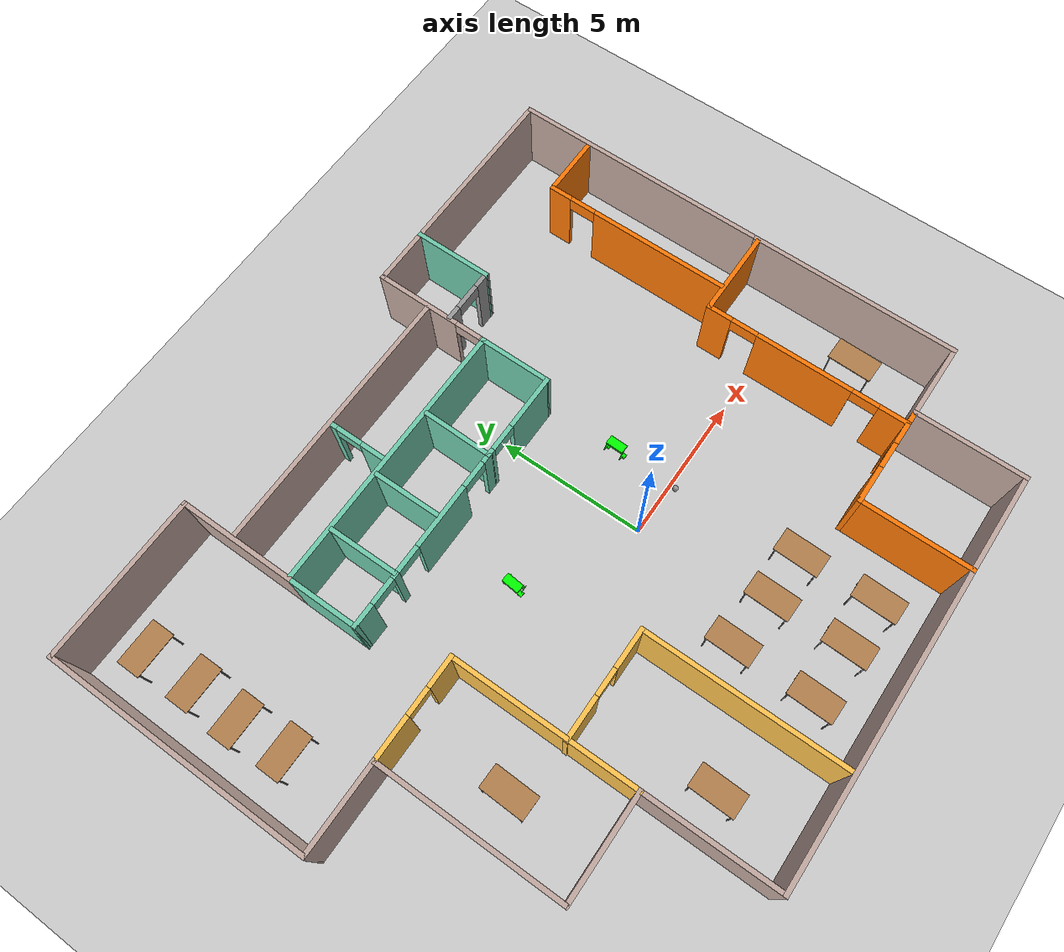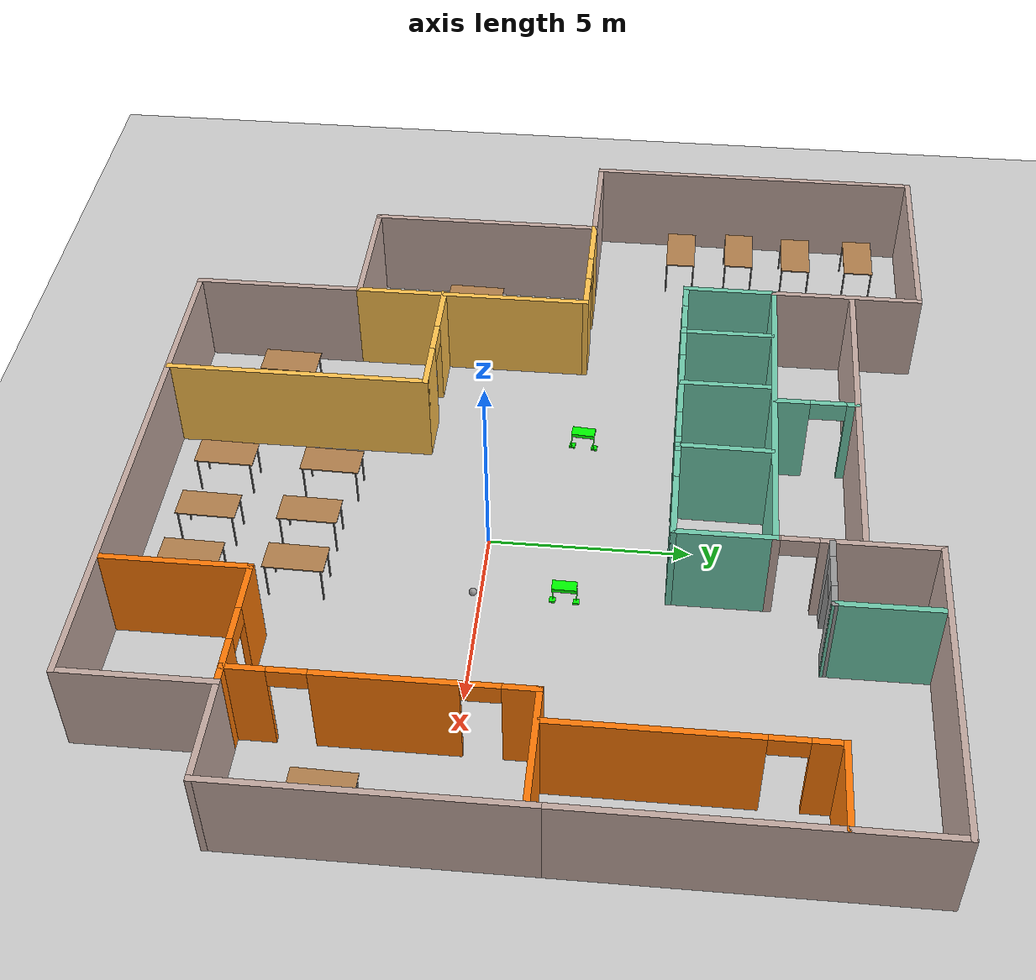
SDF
<sdf version="1.6">
 <world name="default">
  <light name="sun" type="directional">
   <pose>0 0 10 0 -0 0</pose>
   <diffuse>0.8 0.8 0.8 1</diffuse>
   <specular>0.2 0.2 0.2 1</specular>
   <attenuation>
    <range>1000</range>
    <constant>0.9</constant>
    <linear>0.01</linear>
    <quadratic>0.001</quadratic>
   </attenuation>
   <direction>-0.5 0.1 -0.9</direction>
  </light>
  <model name="ground_plane">
   <static>1</static>
   <link name="link">
    <collision name="collision">
     <geometry><plane><normal>0 0 1</normal><size>100 100</size></plane></geometry>
     <surface>
      <contact><collide_bitmask>65535</collide_bitmask></contact>
      <friction><ode><mu>100</mu><mu2>50</mu2></ode></friction>
     </surface>
    </collision>
    <visual name="visual">
     <cast_shadows>0</cast_shadows>
     <geometry><plane><normal>0 0 1</normal><size>100 100</size></plane></geometry>
     <material>
      <script><uri>file://media/materials/scripts/gazebo.material</uri><name>Gazebo/Grey</name></script>
     </material>
    </visual>
   </link>
  </model>
  <gravity>0 0 -9.8</gravity>
  <magnetic_field>6e-06 2.3e-05 -4.2e-05</magnetic_field>
  <atmosphere type="adiabatic"/>
  <physics name="default_physics" default="0" type="ode">
   <max_step_size>0.001</max_step_size>
   <real_time_factor>1</real_time_factor>
   <real_time_update_rate>1000</real_time_update_rate>
  </physics>
  <scene><ambient>0.4 0.4 0.4 1</ambient><background>0.7 0.7 0.7 1</background><shadows>1</shadows></scene>
  <audio><device>default</device></audio>
  <spherical_coordinates>
   <surface_model>EARTH_WGS84</surface_model>
   <latitude_deg>0</latitude_deg>
   <longitude_deg>0</longitude_deg>
   <elevation>0</elevation>
   <heading_deg>0</heading_deg>
  </spherical_coordinates>
  <model name="Office">
   <pose>-1.6791 1.0811 0 0 -0 0</pose>
   <link name="Wall_0">
    <collision name="Wall_0_Collision">
     <geometry><box><size>9 0.15 2.5</size></box></geometry>
     <pose>0 0 1.25 0 -0 0</pose>
    </collision>
    <visual name="Wall_0_Visual">
     <pose>0 0 1.25 0 -0 0</pose>
     <geometry><box><size>9 0.15 2.5</size></box></geometry>
     <material>
      <script><uri>file://media/materials/scripts/gazebo.material</uri><name>Gazebo/Grey</name></script>
      <ambient>0.760784 0.662745 0.627451 1</ambient>
     </material>
     <meta><layer>0</layer></meta>
    </visual>
    <pose>-11.15 5.225 0 0 -0 1.5708</pose>
   </link>
   <link name="Wall_1">
    <collision name="Wall_1_Collision">
     <geometry><box><size>5.5 0.15 2.5</size></box></geometry>
     <pose>0 0 1.25 0 -0 0</pose>
    </collision>
    <visual name="Wall_1_Visual">
     <pose>0 0 1.25 0 -0 0</pose>
     <geometry><box><size>5.5 0.15 2.5</size></box></geometry>
     <material>
      <script><uri>file://media/materials/scripts/gazebo.material</uri><name>Gazebo/Grey</name></script>
      <ambient>0.760784 0.662745 0.627451 1</ambient>
     </material>
     <meta><layer>0</layer></meta>
    </visual>
    <pose>-8.475 9.65 0 0 -0 0</pose>
   </link>
   <link name="Wall_10">
    <collision name="Wall_10_Collision">
     <geometry><box><size>3 0.15 2.5</size></box></geometry>
     <pose>0 0 1.25 0 -0 0</pose>
    </collision>
    <visual name="Wall_10_Visual">
     <pose>0 0 1.25 0 -0 0</pose>
     <geometry><box><size>3 0.15 2.5</size></box></geometry>
     <material>
      <script><uri>file://media/materials/scripts/gazebo.material</uri><name>Gazebo/Grey</name></script>
      <ambient>0.760784 0.662745 0.627451 1</ambient>
     </material>
     <meta><layer>0</layer></meta>
    </visual>
    <pose>-9.725 0.8 0 0 -0 0</pose>
   </link>
   <link name="Wall_11">
    <collision name="Wall_11_Collision">
     <geometry><box><size>6.25 0.15 2.5</size></box></geometry>
     <pose>0 0 1.25 0 -0 0</pose>
    </collision>
    <visual name="Wall_11_Visual">
     <pose>0 0 1.25 0 -0 0</pose>
     <geometry><box><size>6.25 0.15 2.5</size></box></geometry>
     <material>
      <script><uri>file://media/materials/scripts/gazebo.material</uri><name>Gazebo/Grey</name></script>
      <ambient>0.760784 0.662745 0.627451 1</ambient>
     </material>
     <meta><layer>0</layer></meta>
    </visual>
    <pose>-8.3 -2.25 0 0 -0 -1.5708</pose>
   </link>
   <link name="Wall_12">
    <collision name="Wall_12_Collision">
     <geometry><box><size>3.5 0.15 2.5</size></box></geometry>
     <pose>0 0 1.25 0 -0 0</pose>
    </collision>
    <visual name="Wall_12_Visual">
     <pose>0 0 1.25 0 -0 0</pose>
     <geometry><box><size>3.5 0.15 2.5</size></box></geometry>
     <material>
      <script><uri>file://media/materials/scripts/gazebo.material</uri><name>Gazebo/Grey</name></script>
      <ambient>0.760784 0.662745 0.627451 1</ambient>
     </material>
     <meta><layer>0</layer></meta>
    </visual>
    <pose>-6.625 -5.3 0 0 -0 0</pose>
   </link>
   <link name="Wall_13">
    <collision name="Wall_13_Collision">
     <geometry><box><size>4.5 0.15 2.5</size></box></geometry>
     <pose>0 0 1.25 0 -0 0</pose>
    </collision>
    <visual name="Wall_13_Visual">
     <pose>0 0 1.25 0 -0 0</pose>
     <geometry><box><size>4.5 0.15 2.5</size></box></geometry>
     <material>
      <script><uri>file://media/materials/scripts/gazebo.material</uri><name>Gazebo/Grey</name></script>
      <ambient>0.760784 0.662745 0.627451 1</ambient>
     </material>
     <meta><layer>0</layer></meta>
    </visual>
    <pose>-4.95 -7.475 0 0 -0 -1.5708</pose>
   </link>
   <link name="Wall_14">
    <collision name="Wall_14_Collision">
     <geometry><box><size>13.75 0.15 2.5</size></box></geometry>
     <pose>0 0 1.25 0 -0 0</pose>
    </collision>
    <visual name="Wall_14_Visual">
     <pose>0 0 1.25 0 -0 0</pose>
     <geometry><box><size>13.75 0.15 2.5</size></box></geometry>
     <material>
      <script><uri>file://media/materials/scripts/gazebo.material</uri><name>Gazebo/Grey</name></script>
      <ambient>0.760784 0.662745 0.627451 1</ambient>
     </material>
     <meta><layer>0</layer></meta>
    </visual>
    <pose>1.85 -9.65 0 0 -0 0</pose>
   </link>
   <link name="Wall_15">
    <collision name="Wall_15_Collision">
     <geometry><box><size>3.75 0.15 2.5</size></box></geometry>
     <pose>0 0 1.25 0 -0 0</pose>
    </collision>
    <visual name="Wall_15_Visual">
     <pose>0 0 1.25 0 -0 0</pose>
     <geometry><box><size>3.75 0.15 2.5</size></box></geometry>
     <material>
      <script><uri>file://media/materials/scripts/gazebo.material</uri><name>Gazebo/Grey</name></script>
      <ambient>0.760784 0.662745 0.627451 1</ambient>
     </material>
     <meta><layer>0</layer></meta>
    </visual>
    <pose>8.65 -7.85 0 0 -0 1.5708</pose>
   </link>
   <link name="Wall_19">
    <collision name="Wall_19_Collision">
     <geometry><box><size>7.25 0.15 2.5</size></box></geometry>
     <pose>0 0 1.25 0 -0 0</pose>
    </collision>
    <visual name="Wall_19_Visual">
     <pose>0 0 1.25 0 -0 0</pose>
     <geometry><box><size>7.25 0.15 2.5</size></box></geometry>
     <material>
      <script><uri>file://media/materials/scripts/gazebo.material</uri><name>Gazebo/Grey</name></script>
      <ambient>0.760784 0.662745 0.627451 1</ambient>
     </material>
     <meta><layer>0</layer></meta>
    </visual>
    <pose>11.15 -2.5 0 0 -0 -1.5708</pose>
   </link>
   <link name="Wall_2">
    <collision name="Wall_2_Collision">
     <geometry><box><size>4 0.15 2.5</size></box></geometry>
     <pose>0 0 1.25 0 -0 0</pose>
    </collision>
    <visual name="Wall_2_Visual">
     <pose>0 0 1.25 0 -0 0</pose>
     <geometry><box><size>4 0.15 2.5</size></box></geometry>
     <material>
      <script><uri>file://media/materials/scripts/gazebo.material</uri><name>Gazebo/Grey</name></script>
      <ambient>0.760784 0.662745 0.627451 1</ambient>
     </material>
     <meta><layer>0</layer></meta>
    </visual>
    <pose>-5.8 7.725 0 0 -0 -1.5708</pose>
   </link>
   <link name="Wall_20">
    <collision name="Wall_20_Collision">
     <geometry><box><size>2.65 0.15 2.5</size></box></geometry>
     <pose>0 0 1.25 0 -0 0</pose>
    </collision>
    <visual name="Wall_20_Visual">
     <pose>0 0 1.25 0 -0 0</pose>
     <geometry><box><size>2.65 0.15 2.5</size></box></geometry>
     <material>
      <script><uri>file://media/materials/scripts/gazebo.material</uri><name>Gazebo/Grey</name></script>
      <ambient>0.760784 0.662745 0.627451 1</ambient>
     </material>
     <meta><layer>0</layer></meta>
    </visual>
    <pose>9.9 -6.05 0 0 -0 3.14159</pose>
   </link>
   <link name="Wall_22">
    <pose>-6.625 0.8 0 0 -0 0</pose>
    <visual name="Wall_22_Visual_0">
     <pose>-0.996511 0 1.25 0 -0 0</pose>
     <geometry><box><size>1.50698 0.15 2.5</size></box></geometry>
     <material>
      <script><uri>file://media/materials/scripts/gazebo.material</uri><name>Gazebo/Grey</name></script>
      <ambient>1 0.764706 0.305882 1</ambient>
     </material>
     <meta><layer>0</layer></meta>
    </visual>
    <collision name="Wall_22_Collision_0">
     <geometry><box><size>1.50698 0.15 2.5</size></box></geometry>
     <pose>-0.996511 0 1.25 0 -0 0</pose>
    </collision>
    <visual name="Wall_22_Visual_1">
     <pose>1.20349 0 1.25 0 -0 0</pose>
     <geometry><box><size>1.09302 0.15 2.5</size></box></geometry>
     <material>
      <script><uri>file://media/materials/scripts/gazebo.material</uri><name>Gazebo/Grey</name></script>
      <ambient>1 0.764706 0.305882 1</ambient>
     </material>
     <meta><layer>0</layer></meta>
    </visual>
    <collision name="Wall_22_Collision_1">
     <geometry><box><size>1.09302 0.15 2.5</size></box></geometry>
     <pose>1.20349 0 1.25 0 -0 0</pose>
    </collision>
    <visual name="Wall_22_Visual_2">
     <pose>0.206978 0 2.25 0 -0 0</pose>
     <geometry><box><size>0.9 0.15 0.5</size></box></geometry>
     <material>
      <script><uri>file://media/materials/scripts/gazebo.material</uri><name>Gazebo/Grey</name></script>
      <ambient>1 0.764706 0.305882 1</ambient>
     </material>
     <meta><layer>0</layer></meta>
    </visual>
    <collision name="Wall_22_Collision_2">
     <geometry><box><size>0.9 0.15 0.5</size></box></geometry>
     <pose>0.206978 0 2.25 0 -0 0</pose>
    </collision>
   </link>
   <link name="Wall_24">
    <collision name="Wall_24_Collision">
     <geometry><box><size>6.25 0.15 2.5</size></box></geometry>
     <pose>0 0 1.25 0 -0 0</pose>
    </collision>
    <visual name="Wall_24_Visual">
     <pose>0 0 1.25 0 -0 0</pose>
     <geometry><box><size>6.25 0.15 2.5</size></box></geometry>
     <material>
      <script><uri>file://media/materials/scripts/gazebo.material</uri><name>Gazebo/Grey</name></script>
      <ambient>1 0.764706 0.305882 1</ambient>
     </material>
     <meta><layer>0</layer></meta>
    </visual>
    <pose>-4.95 -2.25 0 0 -0 1.5708</pose>
   </link>
   <link name="Wall_26">
    <pose>-3.18284 -3.00704 0 0 -0 0</pose>
    <visual name="Wall_26_Visual_0">
     <pose>-1.13202 0 1.25 0 -0 0</pose>
     <geometry><box><size>1.48596 0.15 2.5</size></box></geometry>
     <material>
      <script><uri>file://media/materials/scripts/gazebo.material</uri><name>Gazebo/Grey</name></script>
      <ambient>1 0.764706 0.305882 1</ambient>
     </material>
     <meta><layer>0</layer></meta>
    </visual>
    <collision name="Wall_26_Collision_0">
     <geometry><box><size>1.48596 0.15 2.5</size></box></geometry>
     <pose>-1.13202 0 1.25 0 -0 0</pose>
    </collision>
    <visual name="Wall_26_Visual_1">
     <pose>1.19298 0 1.25 0 -0 0</pose>
     <geometry><box><size>1.36404 0.15 2.5</size></box></geometry>
     <material>
      <script><uri>file://media/materials/scripts/gazebo.material</uri><name>Gazebo/Grey</name></script>
      <ambient>1 0.764706 0.305882 1</ambient>
     </material>
     <meta><layer>0</layer></meta>
    </visual>
    <collision name="Wall_26_Collision_1">
     <geometry><box><size>1.36404 0.15 2.5</size></box></geometry>
     <pose>1.19298 0 1.25 0 -0 0</pose>
    </collision>
    <visual name="Wall_26_Visual_2">
     <pose>0.060957 0 2.25 0 -0 0</pose>
     <geometry><box><size>0.9 0.15 0.5</size></box></geometry>
     <material>
      <script><uri>file://media/materials/scripts/gazebo.material</uri><name>Gazebo/Grey</name></script>
      <ambient>1 0.764706 0.305882 1</ambient>
     </material>
     <meta><layer>0</layer></meta>
    </visual>
    <collision name="Wall_26_Collision_2">
     <geometry><box><size>0.9 0.15 0.5</size></box></geometry>
     <pose>0.060957 0 2.25 0 -0 0</pose>
    </collision>
   </link>
   <link name="Wall_27">
    <collision name="Wall_27_Collision">
     <geometry><box><size>6.75 0.15 2.5</size></box></geometry>
     <pose>0 0 1.25 0 -0 0</pose>
    </collision>
    <visual name="Wall_27_Visual">
     <pose>0 0 1.25 0 -0 0</pose>
     <geometry><box><size>6.75 0.15 2.5</size></box></geometry>
     <material>
      <script><uri>file://media/materials/scripts/gazebo.material</uri><name>Gazebo/Grey</name></script>
      <ambient>1 0.764706 0.305882 1</ambient>
     </material>
     <meta><layer>0</layer></meta>
    </visual>
    <pose>-1.38284 -6.30704 0 0 -0 -1.5708</pose>
   </link>
   <link name="Wall_3">
    <collision name="Wall_3_Collision">
     <geometry><box><size>9.25 0.15 2.5</size></box></geometry>
     <pose>0 0 1.25 0 -0 0</pose>
    </collision>
    <visual name="Wall_3_Visual">
     <pose>0 0 1.25 0 -0 0</pose>
     <geometry><box><size>9.25 0.15 2.5</size></box></geometry>
     <material>
      <script><uri>file://media/materials/scripts/gazebo.material</uri><name>Gazebo/Grey</name></script>
      <ambient>0.435294 0.796078 0.67451 1</ambient>
     </material>
     <meta><layer>0</layer></meta>
    </visual>
    <pose>-1.25 5.8 0 0 -0 0</pose>
   </link>
   <link name="Wall_31">
    <pose>6.975 -6.05 0 0 -0 3.14159</pose>
    <visual name="Wall_31_Visual_0">
     <pose>-1.11281 0 1.25 0 -0 0</pose>
     <geometry><box><size>1.27439 0.15 2.5</size></box></geometry>
     <material>
      <script><uri>file://media/materials/scripts/gazebo.material</uri><name>Gazebo/Grey</name></script>
      <ambient>0.996078 0.47451 0.0196078 1</ambient>
     </material>
     <meta><layer>0</layer></meta>
    </visual>
    <collision name="Wall_31_Collision_0">
     <geometry><box><size>1.27439 0.15 2.5</size></box></geometry>
     <pose>-1.11281 0 1.25 0 -0 0</pose>
    </collision>
    <visual name="Wall_31_Visual_1">
     <pose>1.08719 0 1.25 0 -0 0</pose>
     <geometry><box><size>1.32561 0.15 2.5</size></box></geometry>
     <material>
      <script><uri>file://media/materials/scripts/gazebo.material</uri><name>Gazebo/Grey</name></script>
      <ambient>0.996078 0.47451 0.0196078 1</ambient>
     </material>
     <meta><layer>0</layer></meta>
    </visual>
    <collision name="Wall_31_Collision_1">
     <geometry><box><size>1.32561 0.15 2.5</size></box></geometry>
     <pose>1.08719 0 1.25 0 -0 0</pose>
    </collision>
    <visual name="Wall_31_Visual_2">
     <pose>-0.025609 0 2.25 0 -0 0</pose>
     <geometry><box><size>0.9 0.15 0.5</size></box></geometry>
     <material>
      <script><uri>file://media/materials/scripts/gazebo.material</uri><name>Gazebo/Grey</name></script>
      <ambient>0.996078 0.47451 0.0196078 1</ambient>
     </material>
     <meta><layer>0</layer></meta>
    </visual>
    <collision name="Wall_31_Collision_2">
     <geometry><box><size>0.9 0.15 0.5</size></box></geometry>
     <pose>-0.025609 0 2.25 0 -0 0</pose>
    </collision>
   </link>
   <link name="Wall_34">
    <collision name="Wall_34_Collision">
     <geometry><box><size>3.75 0.15 2.5</size></box></geometry>
     <pose>0 0 1.25 0 -0 0</pose>
    </collision>
    <visual name="Wall_34_Visual">
     <pose>0 0 1.25 0 -0 0</pose>
     <geometry><box><size>3.75 0.15 2.5</size></box></geometry>
     <material>
      <script><uri>file://media/materials/scripts/gazebo.material</uri><name>Gazebo/Grey</name></script>
      <ambient>0.996078 0.47451 0.0196078 1</ambient>
     </material>
     <meta><layer>0</layer></meta>
    </visual>
    <pose>5.3 -7.85 0 0 -0 -1.5708</pose>
   </link>
   <link name="Wall_36">
    <pose>8.21512 -2.61498 0 0 -0 1.5708</pose>
    <visual name="Wall_36_Visual_0">
     <pose>-2.98655 0 1.25 0 -0 0</pose>
     <geometry><box><size>1.02689 0.15 2.5</size></box></geometry>
     <material>
      <script><uri>file://media/materials/scripts/gazebo.material</uri><name>Gazebo/Grey</name></script>
      <ambient>0.996078 0.47451 0.0196078 1</ambient>
     </material>
     <meta><layer>0</layer></meta>
    </visual>
    <collision name="Wall_36_Collision_0">
     <geometry><box><size>1.02689 0.15 2.5</size></box></geometry>
     <pose>-2.98655 0 1.25 0 -0 0</pose>
    </collision>
    <visual name="Wall_36_Visual_1">
     <pose>0.068841 0 1.25 0 -0 0</pose>
     <geometry><box><size>3.28389 0.15 2.5</size></box></geometry>
     <material>
      <script><uri>file://media/materials/scripts/gazebo.material</uri><name>Gazebo/Grey</name></script>
      <ambient>0.996078 0.47451 0.0196078 1</ambient>
     </material>
     <meta><layer>0</layer></meta>
    </visual>
    <collision name="Wall_36_Collision_1">
     <geometry><box><size>3.28389 0.15 2.5</size></box></geometry>
     <pose>0.068841 0 1.25 0 -0 0</pose>
    </collision>
    <visual name="Wall_36_Visual_2">
     <pose>3.05539 0 1.25 0 -0 0</pose>
     <geometry><box><size>0.889212 0.15 2.5</size></box></geometry>
     <material>
      <script><uri>file://media/materials/scripts/gazebo.material</uri><name>Gazebo/Grey</name></script>
      <ambient>0.996078 0.47451 0.0196078 1</ambient>
     </material>
     <meta><layer>0</layer></meta>
    </visual>
    <collision name="Wall_36_Collision_2">
     <geometry><box><size>0.889212 0.15 2.5</size></box></geometry>
     <pose>3.05539 0 1.25 0 -0 0</pose>
    </collision>
    <visual name="Wall_36_Visual_3">
     <pose>-2.02311 0 2.25 0 -0 0</pose>
     <geometry><box><size>0.9 0.15 0.5</size></box></geometry>
     <material>
      <script><uri>file://media/materials/scripts/gazebo.material</uri><name>Gazebo/Grey</name></script>
      <ambient>0.996078 0.47451 0.0196078 1</ambient>
     </material>
     <meta><layer>0</layer></meta>
    </visual>
    <collision name="Wall_36_Collision_3">
     <geometry><box><size>0.9 0.15 0.5</size></box></geometry>
     <pose>-2.02311 0 2.25 0 -0 0</pose>
    </collision>
    <visual name="Wall_36_Visual_4">
     <pose>2.16079 0 2.25 0 -0 0</pose>
     <geometry><box><size>0.9 0.15 0.5</size></box></geometry>
     <material>
      <script><uri>file://media/materials/scripts/gazebo.material</uri><name>Gazebo/Grey</name></script>
      <ambient>0.996078 0.47451 0.0196078 1</ambient>
     </material>
     <meta><layer>0</layer></meta>
    </visual>
    <collision name="Wall_36_Collision_4">
     <geometry><box><size>0.9 0.15 0.5</size></box></geometry>
     <pose>2.16079 0 2.25 0 -0 0</pose>
    </collision>
   </link>
   <link name="Wall_39">
    <collision name="Wall_39_Collision">
     <geometry><box><size>3 0.15 2.5</size></box></geometry>
     <pose>0 0 1.25 0 -0 0</pose>
    </collision>
    <visual name="Wall_39_Visual">
     <pose>0 0 1.25 0 -0 0</pose>
     <geometry><box><size>3 0.15 2.5</size></box></geometry>
     <material>
      <script><uri>file://media/materials/scripts/gazebo.material</uri><name>Gazebo/Grey</name></script>
      <ambient>0.996078 0.47451 0.0196078 1</ambient>
     </material>
     <meta><layer>0</layer></meta>
    </visual>
    <pose>9.64012 0.810019 0 0 -0 0</pose>
   </link>
   <link name="Wall_4">
    <pose>3.3 7.725 0 0 -0 1.5708</pose>
    <visual name="Wall_4_Visual_0">
     <pose>-1.90552 0 1.25 0 -0 0</pose>
     <geometry><box><size>0.188955 0.15 2.5</size></box></geometry>
     <material>
      <script><uri>file://media/materials/scripts/gazebo.material</uri><name>Gazebo/Grey</name></script>
      <ambient>0.760784 0.662745 0.627451 1</ambient>
     </material>
     <meta><layer>0</layer></meta>
    </visual>
    <collision name="Wall_4_Collision_0">
     <geometry><box><size>0.188955 0.15 2.5</size></box></geometry>
     <pose>-1.90552 0 1.25 0 -0 0</pose>
    </collision>
    <visual name="Wall_4_Visual_1">
     <pose>0.544478 0 1.25 0 -0 0</pose>
     <geometry><box><size>2.91105 0.15 2.5</size></box></geometry>
     <material>
      <script><uri>file://media/materials/scripts/gazebo.material</uri><name>Gazebo/Grey</name></script>
      <ambient>0.760784 0.662745 0.627451 1</ambient>
     </material>
     <meta><layer>0</layer></meta>
    </visual>
    <collision name="Wall_4_Collision_1">
     <geometry><box><size>2.91105 0.15 2.5</size></box></geometry>
     <pose>0.544478 0 1.25 0 -0 0</pose>
    </collision>
    <visual name="Wall_4_Visual_2">
     <pose>-1.36105 0 2.25 0 -0 0</pose>
     <geometry><box><size>0.9 0.15 0.5</size></box></geometry>
     <material>
      <script><uri>file://media/materials/scripts/gazebo.material</uri><name>Gazebo/Grey</name></script>
      <ambient>0.760784 0.662745 0.627451 1</ambient>
     </material>
     <meta><layer>0</layer></meta>
    </visual>
    <collision name="Wall_4_Collision_2">
     <geometry><box><size>0.9 0.15 0.5</size></box></geometry>
     <pose>-1.36105 0 2.25 0 -0 0</pose>
    </collision>
   </link>
   <link name="Wall_41">
    <collision name="Wall_41_Collision">
     <geometry><box><size>9 0.15 2.5</size></box></geometry>
     <pose>0 0 1.25 0 -0 0</pose>
    </collision>
    <visual name="Wall_41_Visual">
     <pose>0 0 1.25 0 -0 0</pose>
     <geometry><box><size>9 0.15 2.5</size></box></geometry>
     <material>
      <script><uri>file://media/materials/scripts/gazebo.material</uri><name>Gazebo/Grey</name></script>
      <ambient>0.760784 0.662745 0.627451 1</ambient>
     </material>
     <meta><layer>0</layer></meta>
    </visual>
    <pose>-1.23454 7.87067 0 0 -0 0</pose>
   </link>
   <link name="Wall_43">
    <pose>-1.47642 6.84275 0 0 -0 -1.5652</pose>
    <visual name="Wall_43_Visual_0">
     <pose>-0.912677 0 1.25 0 -0 0</pose>
     <geometry><box><size>0.333512 0.15 2.5</size></box></geometry>
     <material>
      <script><uri>file://media/materials/scripts/gazebo.material</uri><name>Gazebo/Grey</name></script>
      <ambient>0.435294 0.796078 0.67451 1</ambient>
     </material>
     <meta><layer>0</layer></meta>
    </visual>
    <collision name="Wall_43_Collision_0">
     <geometry><box><size>0.333512 0.15 2.5</size></box></geometry>
     <pose>-0.912677 0 1.25 0 -0 0</pose>
    </collision>
    <visual name="Wall_43_Visual_1">
     <pose>0.616756 0 1.25 0 -0 0</pose>
     <geometry><box><size>0.925354 0.15 2.5</size></box></geometry>
     <material>
      <script><uri>file://media/materials/scripts/gazebo.material</uri><name>Gazebo/Grey</name></script>
      <ambient>0.435294 0.796078 0.67451 1</ambient>
     </material>
     <meta><layer>0</layer></meta>
    </visual>
    <collision name="Wall_43_Collision_1">
     <geometry><box><size>0.925354 0.15 2.5</size></box></geometry>
     <pose>0.616756 0 1.25 0 -0 0</pose>
    </collision>
    <visual name="Wall_43_Visual_2">
     <pose>-0.295921 0 2.25 0 -0 0</pose>
     <geometry><box><size>0.9 0.15 0.5</size></box></geometry>
     <material>
      <script><uri>file://media/materials/scripts/gazebo.material</uri><name>Gazebo/Grey</name></script>
      <ambient>0.435294 0.796078 0.67451 1</ambient>
     </material>
     <meta><layer>0</layer></meta>
    </visual>
    <collision name="Wall_43_Collision_2">
     <geometry><box><size>0.9 0.15 0.5</size></box></geometry>
     <pose>-0.295921 0 2.25 0 -0 0</pose>
    </collision>
   </link>
   <link name="Wall_49">
    <collision name="Wall_49_Collision">
     <geometry><box><size>2.5 0.15 2.5</size></box></geometry>
     <pose>0 0 1.25 0 -0 0</pose>
    </collision>
    <visual name="Wall_49_Visual">
     <pose>0 0 1.25 0 -0 0</pose>
     <geometry><box><size>2.5 0.15 2.5</size></box></geometry>
     <material>
      <script><uri>file://media/materials/scripts/gazebo.material</uri><name>Gazebo/Grey</name></script>
      <ambient>0.435294 0.796078 0.67451 1</ambient>
     </material>
     <meta><layer>0</layer></meta>
    </visual>
    <pose>-5.8 4.625 0 0 -0 -1.5708</pose>
   </link>
   <link name="Wall_5">
    <collision name="Wall_5_Collision">
     <geometry><box><size>8 0.15 2.5</size></box></geometry>
     <pose>0 0 1.25 0 -0 0</pose>
    </collision>
    <visual name="Wall_5_Visual">
     <pose>0 0 1.25 0 -0 0</pose>
     <geometry><box><size>8 0.15 2.5</size></box></geometry>
     <material>
      <script><uri>file://media/materials/scripts/gazebo.material</uri><name>Gazebo/Grey</name></script>
      <ambient>0.760784 0.662745 0.627451 1</ambient>
     </material>
     <meta><layer>0</layer></meta>
    </visual>
    <pose>7.225 9.65 0 0 -0 0</pose>
   </link>
   <link name="Wall_50">
    <pose>-1.25 3.45 0 0 -0 0</pose>
    <visual name="Wall_50_Visual_0">
     <pose>-4.20897 0 1.25 0 -0 0</pose>
     <geometry><box><size>0.832069 0.15 2.5</size></box></geometry>
     <material>
      <script><uri>file://media/materials/scripts/gazebo.material</uri><name>Gazebo/Grey</name></script>
      <ambient>0.435294 0.796078 0.67451 1</ambient>
     </material>
     <meta><layer>0</layer></meta>
    </visual>
    <collision name="Wall_50_Collision_0">
     <geometry><box><size>0.832069 0.15 2.5</size></box></geometry>
     <pose>-4.20897 0 1.25 0 -0 0</pose>
    </collision>
    <visual name="Wall_50_Visual_1">
     <pose>-2.77701 0 1.25 0 -0 0</pose>
     <geometry><box><size>0.231838 0.15 2.5</size></box></geometry>
     <material>
      <script><uri>file://media/materials/scripts/gazebo.material</uri><name>Gazebo/Grey</name></script>
      <ambient>0.435294 0.796078 0.67451 1</ambient>
     </material>
     <meta><layer>0</layer></meta>
    </visual>
    <collision name="Wall_50_Collision_1">
     <geometry><box><size>0.231838 0.15 2.5</size></box></geometry>
     <pose>-2.77701 0 1.25 0 -0 0</pose>
    </collision>
    <visual name="Wall_50_Visual_2">
     <pose>-0.666286 0 1.25 0 -0 0</pose>
     <geometry><box><size>2.18961 0.15 2.5</size></box></geometry>
     <material>
      <script><uri>file://media/materials/scripts/gazebo.material</uri><name>Gazebo/Grey</name></script>
      <ambient>0.435294 0.796078 0.67451 1</ambient>
     </material>
     <meta><layer>0</layer></meta>
    </visual>
    <collision name="Wall_50_Collision_2">
     <geometry><box><size>2.18961 0.15 2.5</size></box></geometry>
     <pose>-0.666286 0 1.25 0 -0 0</pose>
    </collision>
    <visual name="Wall_50_Visual_3">
     <pose>1.5821 0 1.25 0 -0 0</pose>
     <geometry><box><size>0.507151 0.15 2.5</size></box></geometry>
     <material>
      <script><uri>file://media/materials/scripts/gazebo.material</uri><name>Gazebo/Grey</name></script>
      <ambient>0.435294 0.796078 0.67451 1</ambient>
     </material>
     <meta><layer>0</layer></meta>
    </visual>
    <collision name="Wall_50_Collision_3">
     <geometry><box><size>0.507151 0.15 2.5</size></box></geometry>
     <pose>1.5821 0 1.25 0 -0 0</pose>
    </collision>
    <visual name="Wall_50_Visual_4">
     <pose>3.68034 0 1.25 0 -0 0</pose>
     <geometry><box><size>1.88933 0.15 2.5</size></box></geometry>
     <material>
      <script><uri>file://media/materials/scripts/gazebo.material</uri><name>Gazebo/Grey</name></script>
      <ambient>0.435294 0.796078 0.67451 1</ambient>
     </material>
     <meta><layer>0</layer></meta>
    </visual>
    <collision name="Wall_50_Collision_4">
     <geometry><box><size>1.88933 0.15 2.5</size></box></geometry>
     <pose>3.68034 0 1.25 0 -0 0</pose>
    </collision>
    <visual name="Wall_50_Visual_5">
     <pose>-3.34293 0 2.25 0 -0 0</pose>
     <geometry><box><size>0.9 0.15 0.5</size></box></geometry>
     <material>
      <script><uri>file://media/materials/scripts/gazebo.material</uri><name>Gazebo/Grey</name></script>
      <ambient>0.435294 0.796078 0.67451 1</ambient>
     </material>
     <meta><layer>0</layer></meta>
    </visual>
    <collision name="Wall_50_Collision_5">
     <geometry><box><size>0.9 0.15 0.5</size></box></geometry>
     <pose>-3.34293 0 2.25 0 -0 0</pose>
    </collision>
    <visual name="Wall_50_Visual_6">
     <pose>-2.21109 0 2.25 0 -0 0</pose>
     <geometry><box><size>0.9 0.15 0.5</size></box></geometry>
     <material>
      <script><uri>file://media/materials/scripts/gazebo.material</uri><name>Gazebo/Grey</name></script>
      <ambient>0.435294 0.796078 0.67451 1</ambient>
     </material>
     <meta><layer>0</layer></meta>
    </visual>
    <collision name="Wall_50_Collision_6">
     <geometry><box><size>0.9 0.15 0.5</size></box></geometry>
     <pose>-2.21109 0 2.25 0 -0 0</pose>
    </collision>
    <visual name="Wall_50_Visual_7">
     <pose>0.878521 0 2.25 0 -0 0</pose>
     <geometry><box><size>0.9 0.15 0.5</size></box></geometry>
     <material>
      <script><uri>file://media/materials/scripts/gazebo.material</uri><name>Gazebo/Grey</name></script>
      <ambient>0.435294 0.796078 0.67451 1</ambient>
     </material>
     <meta><layer>0</layer></meta>
    </visual>
    <collision name="Wall_50_Collision_7">
     <geometry><box><size>0.9 0.15 0.5</size></box></geometry>
     <pose>0.878521 0 2.25 0 -0 0</pose>
    </collision>
    <visual name="Wall_50_Visual_8">
     <pose>2.28567 0 2.25 0 -0 0</pose>
     <geometry><box><size>0.9 0.15 0.5</size></box></geometry>
     <material>
      <script><uri>file://media/materials/scripts/gazebo.material</uri><name>Gazebo/Grey</name></script>
      <ambient>0.435294 0.796078 0.67451 1</ambient>
     </material>
     <meta><layer>0</layer></meta>
    </visual>
    <collision name="Wall_50_Collision_8">
     <geometry><box><size>0.9 0.15 0.5</size></box></geometry>
     <pose>2.28567 0 2.25 0 -0 0</pose>
    </collision>
   </link>
   <link name="Wall_51">
    <collision name="Wall_51_Collision">
     <geometry><box><size>2.5 0.15 2.5</size></box></geometry>
     <pose>0 0 1.25 0 -0 0</pose>
    </collision>
    <visual name="Wall_51_Visual">
     <pose>0 0 1.25 0 -0 0</pose>
     <geometry><box><size>2.5 0.15 2.5</size></box></geometry>
     <material>
      <script><uri>file://media/materials/scripts/gazebo.material</uri><name>Gazebo/Grey</name></script>
      <ambient>0.435294 0.796078 0.67451 1</ambient>
     </material>
     <meta><layer>0</layer></meta>
    </visual>
    <pose>3.3 4.625 0 0 -0 1.5708</pose>
   </link>
   <link name="Wall_53">
    <collision name="Wall_53_Collision">
     <geometry><box><size>2.36765 0.15 2.5</size></box></geometry>
     <pose>0 0 1.25 0 -0 0</pose>
    </collision>
    <visual name="Wall_53_Visual">
     <pose>0 0 1.25 0 -0 0</pose>
     <geometry><box><size>2.36765 0.15 2.5</size></box></geometry>
     <material>
      <script><uri>file://media/materials/scripts/gazebo.material</uri><name>Gazebo/Grey</name></script>
      <ambient>0.435294 0.796078 0.67451 1</ambient>
     </material>
     <meta><layer>0</layer></meta>
    </visual>
    <pose>-3.9959 4.61011 0 0 -0 -1.56454</pose>
   </link>
   <link name="Wall_55">
    <collision name="Wall_55_Collision">
     <geometry><box><size>2.38765 0.15 2.5</size></box></geometry>
     <pose>0 0 1.25 0 -0 0</pose>
    </collision>
    <visual name="Wall_55_Visual">
     <pose>0 0 1.25 0 -0 0</pose>
     <geometry><box><size>2.38765 0.15 2.5</size></box></geometry>
     <material>
      <script><uri>file://media/materials/scripts/gazebo.material</uri><name>Gazebo/Grey</name></script>
      <ambient>0.435294 0.796078 0.67451 1</ambient>
     </material>
     <meta><layer>0</layer></meta>
    </visual>
    <pose>-1.95572 4.60011 0 0 -0 -1.56476</pose>
   </link>
   <link name="Wall_57">
    <collision name="Wall_57_Collision">
     <geometry><box><size>2.41853 0.15 2.5</size></box></geometry>
     <pose>0 0 1.25 0 -0 0</pose>
    </collision>
    <visual name="Wall_57_Visual">
     <pose>0 0 1.25 0 -0 0</pose>
     <geometry><box><size>2.41853 0.15 2.5</size></box></geometry>
     <material>
      <script><uri>file://media/materials/scripts/gazebo.material</uri><name>Gazebo/Grey</name></script>
      <ambient>0.435294 0.796078 0.67451 1</ambient>
     </material>
     <meta><layer>0</layer></meta>
    </visual>
    <pose>0.382342 4.58472 0 0 -0 -1.58152</pose>
   </link>
   <link name="Wall_59">
    <pose>9.04017 4.07442 0 0 -0 1.5708</pose>
    <visual name="Wall_59_Visual_0">
     <pose>-0.853329 0 1.25 0 -0 0</pose>
     <geometry><box><size>4.79334 0.15 2.5</size></box></geometry>
     <material>
      <script><uri>file://media/materials/scripts/gazebo.material</uri><name>Gazebo/Grey</name></script>
      <ambient>0.996078 0.47451 0.0196078 1</ambient>
     </material>
     <meta><layer>0</layer></meta>
    </visual>
    <collision name="Wall_59_Collision_0">
     <geometry><box><size>4.79334 0.15 2.5</size></box></geometry>
     <pose>-0.853329 0 1.25 0 -0 0</pose>
    </collision>
    <visual name="Wall_59_Visual_1">
     <pose>2.84667 0 1.25 0 -0 0</pose>
     <geometry><box><size>0.806659 0.15 2.5</size></box></geometry>
     <material>
      <script><uri>file://media/materials/scripts/gazebo.material</uri><name>Gazebo/Grey</name></script>
      <ambient>0.996078 0.47451 0.0196078 1</ambient>
     </material>
     <meta><layer>0</layer></meta>
    </visual>
    <collision name="Wall_59_Collision_1">
     <geometry><box><size>0.806659 0.15 2.5</size></box></geometry>
     <pose>2.84667 0 1.25 0 -0 0</pose>
    </collision>
    <visual name="Wall_59_Visual_2">
     <pose>1.99334 0 2.25 0 -0 0</pose>
     <geometry><box><size>0.9 0.15 0.5</size></box></geometry>
     <material>
      <script><uri>file://media/materials/scripts/gazebo.material</uri><name>Gazebo/Grey</name></script>
      <ambient>0.996078 0.47451 0.0196078 1</ambient>
     </material>
     <meta><layer>0</layer></meta>
    </visual>
    <collision name="Wall_59_Collision_2">
     <geometry><box><size>0.9 0.15 0.5</size></box></geometry>
     <pose>1.99334 0 2.25 0 -0 0</pose>
    </collision>
   </link>
   <link name="Wall_6">
    <collision name="Wall_6_Collision">
     <geometry><box><size>8.75 0.15 2.5</size></box></geometry>
     <pose>0 0 1.25 0 -0 0</pose>
    </collision>
    <visual name="Wall_6_Visual">
     <pose>0 0 1.25 0 -0 0</pose>
     <geometry><box><size>8.75 0.15 2.5</size></box></geometry>
     <material>
      <script><uri>file://media/materials/scripts/gazebo.material</uri><name>Gazebo/Grey</name></script>
      <ambient>0.760784 0.662745 0.627451 1</ambient>
     </material>
     <meta><layer>0</layer></meta>
    </visual>
    <pose>11.15 5.35 0 0 -0 -1.5708</pose>
   </link>
   <link name="Wall_60">
    <collision name="Wall_60_Collision">
     <geometry><box><size>2.25 0.15 2.5</size></box></geometry>
     <pose>0 0 1.25 0 -0 0</pose>
    </collision>
    <visual name="Wall_60_Visual">
     <pose>0 0 1.25 0 -0 0</pose>
     <geometry><box><size>2.25 0.15 2.5</size></box></geometry>
     <material>
      <script><uri>file://media/materials/scripts/gazebo.material</uri><name>Gazebo/Grey</name></script>
      <ambient>0.996078 0.47451 0.0196078 1</ambient>
     </material>
     <meta><layer>0</layer></meta>
    </visual>
    <pose>10.0902 7.24942 0 0 -0 0</pose>
   </link>
   <link name="Wall_62">
    <pose>4.27612 7.10309 0 0 -0 0</pose>
    <visual name="Wall_62_Visual_0">
     <pose>-0.747887 0 1.25 0 -0 0</pose>
     <geometry><box><size>0.504226 0.15 2.5</size></box></geometry>
     <material>
      <script><uri>file://media/materials/scripts/gazebo.material</uri><name>Gazebo/Grey</name></script>
      <ambient>1 1 1 1</ambient>
     </material>
     <meta><layer>0</layer></meta>
    </visual>
    <collision name="Wall_62_Collision_0">
     <geometry><box><size>0.504226 0.15 2.5</size></box></geometry>
     <pose>-0.747887 0 1.25 0 -0 0</pose>
    </collision>
    <visual name="Wall_62_Visual_1">
     <pose>0.702113 0 1.25 0 -0 0</pose>
     <geometry><box><size>0.595774 0.15 2.5</size></box></geometry>
     <material>
      <script><uri>file://media/materials/scripts/gazebo.material</uri><name>Gazebo/Grey</name></script>
      <ambient>1 1 1 1</ambient>
     </material>
     <meta><layer>0</layer></meta>
    </visual>
    <collision name="Wall_62_Collision_1">
     <geometry><box><size>0.595774 0.15 2.5</size></box></geometry>
     <pose>0.702113 0 1.25 0 -0 0</pose>
    </collision>
    <visual name="Wall_62_Visual_2">
     <pose>-0.045774 0 2.25 0 -0 0</pose>
     <geometry><box><size>0.9 0.15 0.5</size></box></geometry>
     <material>
      <script><uri>file://media/materials/scripts/gazebo.material</uri><name>Gazebo/Grey</name></script>
      <ambient>1 1 1 1</ambient>
     </material>
     <meta><layer>0</layer></meta>
    </visual>
    <collision name="Wall_62_Collision_2">
     <geometry><box><size>0.9 0.15 0.5</size></box></geometry>
     <pose>-0.045774 0 2.25 0 -0 0</pose>
    </collision>
   </link>
   <link name="Wall_63">
    <collision name="Wall_63_Collision">
     <geometry><box><size>2.68962 0.15 2.5</size></box></geometry>
     <pose>0 0 1.25 0 -0 0</pose>
    </collision>
    <visual name="Wall_63_Visual">
     <pose>0 0 1.25 0 -0 0</pose>
     <geometry><box><size>2.68962 0.15 2.5</size></box></geometry>
     <material>
      <script><uri>file://media/materials/scripts/gazebo.material</uri><name>Gazebo/Grey</name></script>
      <ambient>0.435294 0.796078 0.67451 1</ambient>
     </material>
     <meta><layer>0</layer></meta>
    </visual>
    <pose>5.19834 8.3729 0 0 -0 1.57298</pose>
   </link>
   <static>1</static>
  </model>
  <model name="table">
   <static>1</static>
   <link name="link">
    <collision name="surface">
     <pose>0 0 1 0 -0 0</pose>
     <geometry><box><size>1.5 0.8 0.03</size></box></geometry>
     <surface><friction><ode><mu>0.6</mu><mu2>0.6</mu2></ode></friction></surface>
    </collision>
    <visual name="visual1">
     <pose>0 0 1 0 -0 0</pose>
     <geometry><box><size>1.5 0.8 0.03</size></box></geometry>
     <material>
      <script><uri>file://media/materials/scripts/gazebo.material</uri><name>Gazebo/Wood</name></script>
     </material>
    </visual>
    <collision name="front_left_leg">
     <pose>0.68 0.38 0.5 0 -0 0</pose>
     <geometry><cylinder><radius>0.02</radius><length>1</length></cylinder></geometry>
    </collision>
    <visual name="front_left_leg">
     <pose>0.68 0.38 0.5 0 -0 0</pose>
     <geometry><cylinder><radius>0.02</radius><length>1</length></cylinder></geometry>
     <material>
      <script><uri>file://media/materials/scripts/gazebo.material</uri><name>Gazebo/Grey</name></script>
     </material>
    </visual>
    <collision name="front_right_leg">
     <pose>0.68 -0.38 0.5 0 -0 0</pose>
     <geometry><cylinder><radius>0.02</radius><length>1</length></cylinder></geometry>
    </collision>
    <visual name="front_right_leg">
     <pose>0.68 -0.38 0.5 0 -0 0</pose>
     <geometry><cylinder><radius>0.02</radius><length>1</length></cylinder></geometry>
     <material>
      <script><uri>file://media/materials/scripts/gazebo.material</uri><name>Gazebo/Grey</name></script>
     </material>
    </visual>
    <collision name="back_right_leg">
     <pose>-0.68 -0.38 0.5 0 -0 0</pose>
     <geometry><cylinder><radius>0.02</radius><length>1</length></cylinder></geometry>
    </collision>
    <visual name="back_right_leg">
     <pose>-0.68 -0.38 0.5 0 -0 0</pose>
     <geometry><cylinder><radius>0.02</radius><length>1</length></cylinder></geometry>
     <material>
      <script><uri>file://media/materials/scripts/gazebo.material</uri><name>Gazebo/Grey</name></script>
     </material>
    </visual>
    <collision name="back_left_leg">
     <pose>-0.68 0.38 0.5 0 -0 0</pose>
     <geometry><cylinder><radius>0.02</radius><length>1</length></cylinder></geometry>
    </collision>
    <visual name="back_left_leg">
     <pose>-0.68 0.38 0.5 0 -0 0</pose>
     <geometry><cylinder><radius>0.02</radius><length>1</length></cylinder></geometry>
     <material>
      <script><uri>file://media/materials/scripts/gazebo.material</uri><name>Gazebo/Grey</name></script>
     </material>
    </visual>
   </link>
   <pose>-11.1825 4.34428 0 0 -0 0</pose>
  </model>
  <model name="table_0">
   <static>1</static>
   <link name="link">
    <collision name="surface">
     <pose>0 0 1 0 -0 0</pose>
     <geometry><box><size>1.5 0.8 0.03</size></box></geometry>
     <surface><friction><ode><mu>0.6</mu><mu2>0.6</mu2></ode></friction></surface>
    </collision>
    <visual name="visual1">
     <pose>0 0 1 0 -0 0</pose>
     <geometry><box><size>1.5 0.8 0.03</size></box></geometry>
     <material>
      <script><uri>file://media/materials/scripts/gazebo.material</uri><name>Gazebo/Wood</name></script>
     </material>
    </visual>
    <collision name="front_left_leg">
     <pose>0.68 0.38 0.5 0 -0 0</pose>
     <geometry><cylinder><radius>0.02</radius><length>1</length></cylinder></geometry>
    </collision>
    <visual name="front_left_leg">
     <pose>0.68 0.38 0.5 0 -0 0</pose>
     <geometry><cylinder><radius>0.02</radius><length>1</length></cylinder></geometry>
     <material>
      <script><uri>file://media/materials/scripts/gazebo.material</uri><name>Gazebo/Grey</name></script>
     </material>
    </visual>
    <collision name="front_right_leg">
     <pose>0.68 -0.38 0.5 0 -0 0</pose>
     <geometry><cylinder><radius>0.02</radius><length>1</length></cylinder></geometry>
    </collision>
    <visual name="front_right_leg">
     <pose>0.68 -0.38 0.5 0 -0 0</pose>
     <geometry><cylinder><radius>0.02</radius><length>1</length></cylinder></geometry>
     <material>
      <script><uri>file://media/materials/scripts/gazebo.material</uri><name>Gazebo/Grey</name></script>
     </material>
    </visual>
    <collision name="back_right_leg">
     <pose>-0.68 -0.38 0.5 0 -0 0</pose>
     <geometry><cylinder><radius>0.02</radius><length>1</length></cylinder></geometry>
    </collision>
    <visual name="back_right_leg">
     <pose>-0.68 -0.38 0.5 0 -0 0</pose>
     <geometry><cylinder><radius>0.02</radius><length>1</length></cylinder></geometry>
     <material>
      <script><uri>file://media/materials/scripts/gazebo.material</uri><name>Gazebo/Grey</name></script>
     </material>
    </visual>
    <collision name="back_left_leg">
     <pose>-0.68 0.38 0.5 0 -0 0</pose>
     <geometry><cylinder><radius>0.02</radius><length>1</length></cylinder></geometry>
    </collision>
    <visual name="back_left_leg">
     <pose>-0.68 0.38 0.5 0 -0 0</pose>
     <geometry><cylinder><radius>0.02</radius><length>1</length></cylinder></geometry>
     <material>
      <script><uri>file://media/materials/scripts/gazebo.material</uri><name>Gazebo/Grey</name></script>
     </material>
    </visual>
   </link>
   <pose>-11.2802 6.01206 0 0 -0 0</pose>
  </model>
  <model name="table_1">
   <static>1</static>
   <link name="link">
    <collision name="surface">
     <pose>0 0 1 0 -0 0</pose>
     <geometry><box><size>1.5 0.8 0.03</size></box></geometry>
     <surface><friction><ode><mu>0.6</mu><mu2>0.6</mu2></ode></friction></surface>
    </collision>
    <visual name="visual1">
     <pose>0 0 1 0 -0 0</pose>
     <geometry><box><size>1.5 0.8 0.03</size></box></geometry>
     <material>
      <script><uri>file://media/materials/scripts/gazebo.material</uri><name>Gazebo/Wood</name></script>
     </material>
    </visual>
    <collision name="front_left_leg">
     <pose>0.68 0.38 0.5 0 -0 0</pose>
     <geometry><cylinder><radius>0.02</radius><length>1</length></cylinder></geometry>
    </collision>
    <visual name="front_left_leg">
     <pose>0.68 0.38 0.5 0 -0 0</pose>
     <geometry><cylinder><radius>0.02</radius><length>1</length></cylinder></geometry>
     <material>
      <script><uri>file://media/materials/scripts/gazebo.material</uri><name>Gazebo/Grey</name></script>
     </material>
    </visual>
    <collision name="front_right_leg">
     <pose>0.68 -0.38 0.5 0 -0 0</pose>
     <geometry><cylinder><radius>0.02</radius><length>1</length></cylinder></geometry>
    </collision>
    <visual name="front_right_leg">
     <pose>0.68 -0.38 0.5 0 -0 0</pose>
     <geometry><cylinder><radius>0.02</radius><length>1</length></cylinder></geometry>
     <material>
      <script><uri>file://media/materials/scripts/gazebo.material</uri><name>Gazebo/Grey</name></script>
     </material>
    </visual>
    <collision name="back_right_leg">
     <pose>-0.68 -0.38 0.5 0 -0 0</pose>
     <geometry><cylinder><radius>0.02</radius><length>1</length></cylinder></geometry>
    </collision>
    <visual name="back_right_leg">
     <pose>-0.68 -0.38 0.5 0 -0 0</pose>
     <geometry><cylinder><radius>0.02</radius><length>1</length></cylinder></geometry>
     <material>
      <script><uri>file://media/materials/scripts/gazebo.material</uri><name>Gazebo/Grey</name></script>
     </material>
    </visual>
    <collision name="back_left_leg">
     <pose>-0.68 0.38 0.5 0 -0 0</pose>
     <geometry><cylinder><radius>0.02</radius><length>1</length></cylinder></geometry>
    </collision>
    <visual name="back_left_leg">
     <pose>-0.68 0.38 0.5 0 -0 0</pose>
     <geometry><cylinder><radius>0.02</radius><length>1</length></cylinder></geometry>
     <material>
      <script><uri>file://media/materials/scripts/gazebo.material</uri><name>Gazebo/Grey</name></script>
     </material>
    </visual>
   </link>
   <pose>-11.2069 7.63784 0 0 -0 0</pose>
  </model>
  <model name="table_2">
   <static>1</static>
   <link name="link">
    <collision name="surface">
     <pose>0 0 1 0 -0 0</pose>
     <geometry><box><size>1.5 0.8 0.03</size></box></geometry>
     <surface><friction><ode><mu>0.6</mu><mu2>0.6</mu2></ode></friction></surface>
    </collision>
    <visual name="visual1">
     <pose>0 0 1 0 -0 0</pose>
     <geometry><box><size>1.5 0.8 0.03</size></box></geometry>
     <material>
      <script><uri>file://media/materials/scripts/gazebo.material</uri><name>Gazebo/Wood</name></script>
     </material>
    </visual>
    <collision name="front_left_leg">
     <pose>0.68 0.38 0.5 0 -0 0</pose>
     <geometry><cylinder><radius>0.02</radius><length>1</length></cylinder></geometry>
    </collision>
    <visual name="front_left_leg">
     <pose>0.68 0.38 0.5 0 -0 0</pose>
     <geometry><cylinder><radius>0.02</radius><length>1</length></cylinder></geometry>
     <material>
      <script><uri>file://media/materials/scripts/gazebo.material</uri><name>Gazebo/Grey</name></script>
     </material>
    </visual>
    <collision name="front_right_leg">
     <pose>0.68 -0.38 0.5 0 -0 0</pose>
     <geometry><cylinder><radius>0.02</radius><length>1</length></cylinder></geometry>
    </collision>
    <visual name="front_right_leg">
     <pose>0.68 -0.38 0.5 0 -0 0</pose>
     <geometry><cylinder><radius>0.02</radius><length>1</length></cylinder></geometry>
     <material>
      <script><uri>file://media/materials/scripts/gazebo.material</uri><name>Gazebo/Grey</name></script>
     </material>
    </visual>
    <collision name="back_right_leg">
     <pose>-0.68 -0.38 0.5 0 -0 0</pose>
     <geometry><cylinder><radius>0.02</radius><length>1</length></cylinder></geometry>
    </collision>
    <visual name="back_right_leg">
     <pose>-0.68 -0.38 0.5 0 -0 0</pose>
     <geometry><cylinder><radius>0.02</radius><length>1</length></cylinder></geometry>
     <material>
      <script><uri>file://media/materials/scripts/gazebo.material</uri><name>Gazebo/Grey</name></script>
     </material>
    </visual>
    <collision name="back_left_leg">
     <pose>-0.68 0.38 0.5 0 -0 0</pose>
     <geometry><cylinder><radius>0.02</radius><length>1</length></cylinder></geometry>
    </collision>
    <visual name="back_left_leg">
     <pose>-0.68 0.38 0.5 0 -0 0</pose>
     <geometry><cylinder><radius>0.02</radius><length>1</length></cylinder></geometry>
     <material>
      <script><uri>file://media/materials/scripts/gazebo.material</uri><name>Gazebo/Grey</name></script>
     </material>
    </visual>
   </link>
   <pose>-11.2522 9.42213 0 0 -0 0</pose>
  </model>
  <model name="table_3">
   <static>1</static>
   <link name="link">
    <collision name="surface">
     <pose>0 0 1 0 -0 0</pose>
     <geometry><box><size>1.5 0.8 0.03</size></box></geometry>
     <surface><friction><ode><mu>0.6</mu><mu2>0.6</mu2></ode></friction></surface>
    </collision>
    <visual name="visual1">
     <pose>0 0 1 0 -0 0</pose>
     <geometry><box><size>1.5 0.8 0.03</size></box></geometry>
     <material>
      <script><uri>file://media/materials/scripts/gazebo.material</uri><name>Gazebo/Wood</name></script>
     </material>
    </visual>
    <collision name="front_left_leg">
     <pose>0.68 0.38 0.5 0 -0 0</pose>
     <geometry><cylinder><radius>0.02</radius><length>1</length></cylinder></geometry>
    </collision>
    <visual name="front_left_leg">
     <pose>0.68 0.38 0.5 0 -0 0</pose>
     <geometry><cylinder><radius>0.02</radius><length>1</length></cylinder></geometry>
     <material>
      <script><uri>file://media/materials/scripts/gazebo.material</uri><name>Gazebo/Grey</name></script>
     </material>
    </visual>
    <collision name="front_right_leg">
     <pose>0.68 -0.38 0.5 0 -0 0</pose>
     <geometry><cylinder><radius>0.02</radius><length>1</length></cylinder></geometry>
    </collision>
    <visual name="front_right_leg">
     <pose>0.68 -0.38 0.5 0 -0 0</pose>
     <geometry><cylinder><radius>0.02</radius><length>1</length></cylinder></geometry>
     <material>
      <script><uri>file://media/materials/scripts/gazebo.material</uri><name>Gazebo/Grey</name></script>
     </material>
    </visual>
    <collision name="back_right_leg">
     <pose>-0.68 -0.38 0.5 0 -0 0</pose>
     <geometry><cylinder><radius>0.02</radius><length>1</length></cylinder></geometry>
    </collision>
    <visual name="back_right_leg">
     <pose>-0.68 -0.38 0.5 0 -0 0</pose>
     <geometry><cylinder><radius>0.02</radius><length>1</length></cylinder></geometry>
     <material>
      <script><uri>file://media/materials/scripts/gazebo.material</uri><name>Gazebo/Grey</name></script>
     </material>
    </visual>
    <collision name="back_left_leg">
     <pose>-0.68 0.38 0.5 0 -0 0</pose>
     <geometry><cylinder><radius>0.02</radius><length>1</length></cylinder></geometry>
    </collision>
    <visual name="back_left_leg">
     <pose>-0.68 0.38 0.5 0 -0 0</pose>
     <geometry><cylinder><radius>0.02</radius><length>1</length></cylinder></geometry>
     <material>
      <script><uri>file://media/materials/scripts/gazebo.material</uri><name>Gazebo/Grey</name></script>
     </material>
    </visual>
   </link>
   <pose>-1.5427 -6.87927 0 0 -0 1.54837</pose>
  </model>
  <model name="table_3_clone">
   <static>1</static>
   <link name="link">
    <collision name="surface">
     <pose>0 0 1 0 -0 0</pose>
     <geometry><box><size>1.5 0.8 0.03</size></box></geometry>
     <surface><friction><ode><mu>0.6</mu><mu2>0.6</mu2></ode></friction></surface>
    </collision>
    <visual name="visual1">
     <pose>0 0 1 0 -0 0</pose>
     <geometry><box><size>1.5 0.8 0.03</size></box></geometry>
     <material>
      <script><uri>file://media/materials/scripts/gazebo.material</uri><name>Gazebo/Wood</name></script>
     </material>
    </visual>
    <collision name="front_left_leg">
     <pose>0.68 0.38 0.5 0 -0 0</pose>
     <geometry><cylinder><radius>0.02</radius><length>1</length></cylinder></geometry>
    </collision>
    <visual name="front_left_leg">
     <pose>0.68 0.38 0.5 0 -0 0</pose>
     <geometry><cylinder><radius>0.02</radius><length>1</length></cylinder></geometry>
     <material>
      <script><uri>file://media/materials/scripts/gazebo.material</uri><name>Gazebo/Grey</name></script>
     </material>
    </visual>
    <collision name="front_right_leg">
     <pose>0.68 -0.38 0.5 0 -0 0</pose>
     <geometry><cylinder><radius>0.02</radius><length>1</length></cylinder></geometry>
    </collision>
    <visual name="front_right_leg">
     <pose>0.68 -0.38 0.5 0 -0 0</pose>
     <geometry><cylinder><radius>0.02</radius><length>1</length></cylinder></geometry>
     <material>
      <script><uri>file://media/materials/scripts/gazebo.material</uri><name>Gazebo/Grey</name></script>
     </material>
    </visual>
    <collision name="back_right_leg">
     <pose>-0.68 -0.38 0.5 0 -0 0</pose>
     <geometry><cylinder><radius>0.02</radius><length>1</length></cylinder></geometry>
    </collision>
    <visual name="back_right_leg">
     <pose>-0.68 -0.38 0.5 0 -0 0</pose>
     <geometry><cylinder><radius>0.02</radius><length>1</length></cylinder></geometry>
     <material>
      <script><uri>file://media/materials/scripts/gazebo.material</uri><name>Gazebo/Grey</name></script>
     </material>
    </visual>
    <collision name="back_left_leg">
     <pose>-0.68 0.38 0.5 0 -0 0</pose>
     <geometry><cylinder><radius>0.02</radius><length>1</length></cylinder></geometry>
    </collision>
    <visual name="back_left_leg">
     <pose>-0.68 0.38 0.5 0 -0 0</pose>
     <geometry><cylinder><radius>0.02</radius><length>1</length></cylinder></geometry>
     <material>
      <script><uri>file://media/materials/scripts/gazebo.material</uri><name>Gazebo/Grey</name></script>
     </material>
    </visual>
   </link>
   <pose>-1.51069 -4.16084 0 0 -0 1.54837</pose>
  </model>
  <model name="table_3_clone_0">
   <static>1</static>
   <link name="link">
    <collision name="surface">
     <pose>0 0 1 0 -0 0</pose>
     <geometry><box><size>1.5 0.8 0.03</size></box></geometry>
     <surface><friction><ode><mu>0.6</mu><mu2>0.6</mu2></ode></friction></surface>
    </collision>
    <visual name="visual1">
     <pose>0 0 1 0 -0 0</pose>
     <geometry><box><size>1.5 0.8 0.03</size></box></geometry>
     <material>
      <script><uri>file://media/materials/scripts/gazebo.material</uri><name>Gazebo/Wood</name></script>
     </material>
    </visual>
    <collision name="front_left_leg">
     <pose>0.68 0.38 0.5 0 -0 0</pose>
     <geometry><cylinder><radius>0.02</radius><length>1</length></cylinder></geometry>
    </collision>
    <visual name="front_left_leg">
     <pose>0.68 0.38 0.5 0 -0 0</pose>
     <geometry><cylinder><radius>0.02</radius><length>1</length></cylinder></geometry>
     <material>
      <script><uri>file://media/materials/scripts/gazebo.material</uri><name>Gazebo/Grey</name></script>
     </material>
    </visual>
    <collision name="front_right_leg">
     <pose>0.68 -0.38 0.5 0 -0 0</pose>
     <geometry><cylinder><radius>0.02</radius><length>1</length></cylinder></geometry>
    </collision>
    <visual name="front_right_leg">
     <pose>0.68 -0.38 0.5 0 -0 0</pose>
     <geometry><cylinder><radius>0.02</radius><length>1</length></cylinder></geometry>
     <material>
      <script><uri>file://media/materials/scripts/gazebo.material</uri><name>Gazebo/Grey</name></script>
     </material>
    </visual>
    <collision name="back_right_leg">
     <pose>-0.68 -0.38 0.5 0 -0 0</pose>
     <geometry><cylinder><radius>0.02</radius><length>1</length></cylinder></geometry>
    </collision>
    <visual name="back_right_leg">
     <pose>-0.68 -0.38 0.5 0 -0 0</pose>
     <geometry><cylinder><radius>0.02</radius><length>1</length></cylinder></geometry>
     <material>
      <script><uri>file://media/materials/scripts/gazebo.material</uri><name>Gazebo/Grey</name></script>
     </material>
    </visual>
    <collision name="back_left_leg">
     <pose>-0.68 0.38 0.5 0 -0 0</pose>
     <geometry><cylinder><radius>0.02</radius><length>1</length></cylinder></geometry>
    </collision>
    <visual name="back_left_leg">
     <pose>-0.68 0.38 0.5 0 -0 0</pose>
     <geometry><cylinder><radius>0.02</radius><length>1</length></cylinder></geometry>
     <material>
      <script><uri>file://media/materials/scripts/gazebo.material</uri><name>Gazebo/Grey</name></script>
     </material>
    </visual>
   </link>
   <pose>0.323979 -6.91935 0 0 -0 1.54837</pose>
  </model>
  <model name="table_3_clone_1">
   <static>1</static>
   <link name="link">
    <collision name="surface">
     <pose>0 0 1 0 -0 0</pose>
     <geometry><box><size>1.5 0.8 0.03</size></box></geometry>
     <surface><friction><ode><mu>0.6</mu><mu2>0.6</mu2></ode></friction></surface>
    </collision>
    <visual name="visual1">
     <pose>0 0 1 0 -0 0</pose>
     <geometry><box><size>1.5 0.8 0.03</size></box></geometry>
     <material>
      <script><uri>file://media/materials/scripts/gazebo.material</uri><name>Gazebo/Wood</name></script>
     </material>
    </visual>
    <collision name="front_left_leg">
     <pose>0.68 0.38 0.5 0 -0 0</pose>
     <geometry><cylinder><radius>0.02</radius><length>1</length></cylinder></geometry>
    </collision>
    <visual name="front_left_leg">
     <pose>0.68 0.38 0.5 0 -0 0</pose>
     <geometry><cylinder><radius>0.02</radius><length>1</length></cylinder></geometry>
     <material>
      <script><uri>file://media/materials/scripts/gazebo.material</uri><name>Gazebo/Grey</name></script>
     </material>
    </visual>
    <collision name="front_right_leg">
     <pose>0.68 -0.38 0.5 0 -0 0</pose>
     <geometry><cylinder><radius>0.02</radius><length>1</length></cylinder></geometry>
    </collision>
    <visual name="front_right_leg">
     <pose>0.68 -0.38 0.5 0 -0 0</pose>
     <geometry><cylinder><radius>0.02</radius><length>1</length></cylinder></geometry>
     <material>
      <script><uri>file://media/materials/scripts/gazebo.material</uri><name>Gazebo/Grey</name></script>
     </material>
    </visual>
    <collision name="back_right_leg">
     <pose>-0.68 -0.38 0.5 0 -0 0</pose>
     <geometry><cylinder><radius>0.02</radius><length>1</length></cylinder></geometry>
    </collision>
    <visual name="back_right_leg">
     <pose>-0.68 -0.38 0.5 0 -0 0</pose>
     <geometry><cylinder><radius>0.02</radius><length>1</length></cylinder></geometry>
     <material>
      <script><uri>file://media/materials/scripts/gazebo.material</uri><name>Gazebo/Grey</name></script>
     </material>
    </visual>
    <collision name="back_left_leg">
     <pose>-0.68 0.38 0.5 0 -0 0</pose>
     <geometry><cylinder><radius>0.02</radius><length>1</length></cylinder></geometry>
    </collision>
    <visual name="back_left_leg">
     <pose>-0.68 0.38 0.5 0 -0 0</pose>
     <geometry><cylinder><radius>0.02</radius><length>1</length></cylinder></geometry>
     <material>
      <script><uri>file://media/materials/scripts/gazebo.material</uri><name>Gazebo/Grey</name></script>
     </material>
    </visual>
   </link>
   <pose>0.270182 -4.39298 0 0 -0 1.54837</pose>
  </model>
  <model name="table_3_clone_2">
   <static>1</static>
   <link name="link">
    <collision name="surface">
     <pose>0 0 1 0 -0 0</pose>
     <geometry><box><size>1.5 0.8 0.03</size></box></geometry>
     <surface><friction><ode><mu>0.6</mu><mu2>0.6</mu2></ode></friction></surface>
    </collision>
    <visual name="visual1">
     <pose>0 0 1 0 -0 0</pose>
     <geometry><box><size>1.5 0.8 0.03</size></box></geometry>
     <material>
      <script><uri>file://media/materials/scripts/gazebo.material</uri><name>Gazebo/Wood</name></script>
     </material>
    </visual>
    <collision name="front_left_leg">
     <pose>0.68 0.38 0.5 0 -0 0</pose>
     <geometry><cylinder><radius>0.02</radius><length>1</length></cylinder></geometry>
    </collision>
    <visual name="front_left_leg">
     <pose>0.68 0.38 0.5 0 -0 0</pose>
     <geometry><cylinder><radius>0.02</radius><length>1</length></cylinder></geometry>
     <material>
      <script><uri>file://media/materials/scripts/gazebo.material</uri><name>Gazebo/Grey</name></script>
     </material>
    </visual>
    <collision name="front_right_leg">
     <pose>0.68 -0.38 0.5 0 -0 0</pose>
     <geometry><cylinder><radius>0.02</radius><length>1</length></cylinder></geometry>
    </collision>
    <visual name="front_right_leg">
     <pose>0.68 -0.38 0.5 0 -0 0</pose>
     <geometry><cylinder><radius>0.02</radius><length>1</length></cylinder></geometry>
     <material>
      <script><uri>file://media/materials/scripts/gazebo.material</uri><name>Gazebo/Grey</name></script>
     </material>
    </visual>
    <collision name="back_right_leg">
     <pose>-0.68 -0.38 0.5 0 -0 0</pose>
     <geometry><cylinder><radius>0.02</radius><length>1</length></cylinder></geometry>
    </collision>
    <visual name="back_right_leg">
     <pose>-0.68 -0.38 0.5 0 -0 0</pose>
     <geometry><cylinder><radius>0.02</radius><length>1</length></cylinder></geometry>
     <material>
      <script><uri>file://media/materials/scripts/gazebo.material</uri><name>Gazebo/Grey</name></script>
     </material>
    </visual>
    <collision name="back_left_leg">
     <pose>-0.68 0.38 0.5 0 -0 0</pose>
     <geometry><cylinder><radius>0.02</radius><length>1</length></cylinder></geometry>
    </collision>
    <visual name="back_left_leg">
     <pose>-0.68 0.38 0.5 0 -0 0</pose>
     <geometry><cylinder><radius>0.02</radius><length>1</length></cylinder></geometry>
     <material>
      <script><uri>file://media/materials/scripts/gazebo.material</uri><name>Gazebo/Grey</name></script>
     </material>
    </visual>
   </link>
   <pose>1.96463 -6.97316 0 0 -0 1.54837</pose>
  </model>
  <model name="table_3_clone_3">
   <static>1</static>
   <link name="link">
    <collision name="surface">
     <pose>0 0 1 0 -0 0</pose>
     <geometry><box><size>1.5 0.8 0.03</size></box></geometry>
     <surface><friction><ode><mu>0.6</mu><mu2>0.6</mu2></ode></friction></surface>
    </collision>
    <visual name="visual1">
     <pose>0 0 1 0 -0 0</pose>
     <geometry><box><size>1.5 0.8 0.03</size></box></geometry>
     <material>
      <script><uri>file://media/materials/scripts/gazebo.material</uri><name>Gazebo/Wood</name></script>
     </material>
    </visual>
    <collision name="front_left_leg">
     <pose>0.68 0.38 0.5 0 -0 0</pose>
     <geometry><cylinder><radius>0.02</radius><length>1</length></cylinder></geometry>
    </collision>
    <visual name="front_left_leg">
     <pose>0.68 0.38 0.5 0 -0 0</pose>
     <geometry><cylinder><radius>0.02</radius><length>1</length></cylinder></geometry>
     <material>
      <script><uri>file://media/materials/scripts/gazebo.material</uri><name>Gazebo/Grey</name></script>
     </material>
    </visual>
    <collision name="front_right_leg">
     <pose>0.68 -0.38 0.5 0 -0 0</pose>
     <geometry><cylinder><radius>0.02</radius><length>1</length></cylinder></geometry>
    </collision>
    <visual name="front_right_leg">
     <pose>0.68 -0.38 0.5 0 -0 0</pose>
     <geometry><cylinder><radius>0.02</radius><length>1</length></cylinder></geometry>
     <material>
      <script><uri>file://media/materials/scripts/gazebo.material</uri><name>Gazebo/Grey</name></script>
     </material>
    </visual>
    <collision name="back_right_leg">
     <pose>-0.68 -0.38 0.5 0 -0 0</pose>
     <geometry><cylinder><radius>0.02</radius><length>1</length></cylinder></geometry>
    </collision>
    <visual name="back_right_leg">
     <pose>-0.68 -0.38 0.5 0 -0 0</pose>
     <geometry><cylinder><radius>0.02</radius><length>1</length></cylinder></geometry>
     <material>
      <script><uri>file://media/materials/scripts/gazebo.material</uri><name>Gazebo/Grey</name></script>
     </material>
    </visual>
    <collision name="back_left_leg">
     <pose>-0.68 0.38 0.5 0 -0 0</pose>
     <geometry><cylinder><radius>0.02</radius><length>1</length></cylinder></geometry>
    </collision>
    <visual name="back_left_leg">
     <pose>-0.68 0.38 0.5 0 -0 0</pose>
     <geometry><cylinder><radius>0.02</radius><length>1</length></cylinder></geometry>
     <material>
      <script><uri>file://media/materials/scripts/gazebo.material</uri><name>Gazebo/Grey</name></script>
     </material>
    </visual>
   </link>
   <pose>1.89535 -4.42067 0 0 -0 1.54837</pose>
  </model>
  <model name="humanoid_robot">
   <link name="link_10">
    <inertial>
     <mass>10</mass>
     <inertia>
      <ixx>0.166667</ixx>
      <ixy>0</ixy>
      <ixz>0</ixz>
      <iyy>0.166667</iyy>
      <iyz>0</iyz>
      <izz>0.166667</izz>
     </inertia>
    </inertial>
    <pose>-0.193692 0.719799 0.180001 -0 -0 -0</pose>
    <visual name="visual">
     <geometry><box><size>0.15 0.15 0.05</size></box></geometry>
     <material>
      <lighting>1</lighting>
      <script><uri>file://media/materials/scripts/gazebo.material</uri><name>Gazebo/Grey</name></script>
      <shader type="vertex"><normal_map>__default__</normal_map></shader>
      <ambient>0 1 0 1</ambient>
      <diffuse>0.7 0.7 0.7 1</diffuse>
      <specular>0.01 0.01 0.01 1</specular>
      <emissive>0 0 0 1</emissive>
     </material>
    </visual>
    <collision name="collision">
     <geometry><box><size>0.15 0.15 0.05</size></box></geometry>
     <surface>
      <friction>
       <ode><mu>1</mu><mu2>1</mu2><fdir1>0 0 0</fdir1><slip1>0</slip1><slip2>0</slip2></ode>
       <torsional>
        <coefficient>1</coefficient>
        <patch_radius>0</patch_radius>
        <surface_radius>0</surface_radius>
        <use_patch_radius>1</use_patch_radius>
        <ode><slip>0</slip></ode>
       </torsional>
      </friction>
      <bounce><restitution_coefficient>0</restitution_coefficient><threshold>1e+06</threshold></bounce>
      <contact>
       <collide_without_contact>0</collide_without_contact>
       <collide_without_contact_bitmask>1</collide_without_contact_bitmask>
       <collide_bitmask>1</collide_bitmask>
       <ode>
        <soft_cfm>0</soft_cfm>
        <soft_erp>0.2</soft_erp>
        <kp>1e+13</kp>
        <kd>1</kd>
        <max_vel>0.01</max_vel>
        <min_depth>0</min_depth>
       </ode>
       <bullet>
        <split_impulse>1</split_impulse>
        <split_impulse_penetration_threshold>-0.01</split_impulse_penetration_threshold>
        <soft_cfm>0</soft_cfm>
        <soft_erp>0.2</soft_erp>
        <kp>1e+13</kp>
        <kd>1</kd>
       </bullet>
      </contact>
     </surface>
    </collision>
   </link>
   <link name="link_10_clone">
    <inertial>
     <mass>10</mass>
     <inertia>
      <ixx>0.166667</ixx>
      <ixy>0</ixy>
      <ixz>0</ixz>
      <iyy>0.166667</iyy>
      <iyz>0</iyz>
      <izz>0.166667</izz>
     </inertia>
    </inertial>
    <pose>-0.193692 0.139799 0.180001 -0 -0 -0</pose>
    <visual name="visual">
     <geometry><box><size>0.15 0.15 0.05</size></box></geometry>
     <material>
      <lighting>1</lighting>
      <script><uri>file://media/materials/scripts/gazebo.material</uri><name>Gazebo/Grey</name></script>
      <shader type="vertex"><normal_map>__default__</normal_map></shader>
      <ambient>0 1 0 1</ambient>
      <diffuse>0.7 0.7 0.7 1</diffuse>
      <specular>0.01 0.01 0.01 1</specular>
      <emissive>0 0 0 1</emissive>
     </material>
    </visual>
    <collision name="collision">
     <geometry><box><size>0.15 0.15 0.05</size></box></geometry>
     <surface>
      <friction>
       <ode><mu>1</mu><mu2>1</mu2><fdir1>0 0 0</fdir1><slip1>0</slip1><slip2>0</slip2></ode>
       <torsional>
        <coefficient>1</coefficient>
        <patch_radius>0</patch_radius>
        <surface_radius>0</surface_radius>
        <use_patch_radius>1</use_patch_radius>
        <ode><slip>0</slip></ode>
       </torsional>
      </friction>
      <bounce><restitution_coefficient>0</restitution_coefficient><threshold>1e+06</threshold></bounce>
      <contact>
       <collide_without_contact>0</collide_without_contact>
       <collide_without_contact_bitmask>1</collide_without_contact_bitmask>
       <collide_bitmask>1</collide_bitmask>
       <ode>
        <soft_cfm>0</soft_cfm>
        <soft_erp>0.2</soft_erp>
        <kp>1e+13</kp>
        <kd>1</kd>
        <max_vel>0.01</max_vel>
        <min_depth>0</min_depth>
       </ode>
       <bullet>
        <split_impulse>1</split_impulse>
        <split_impulse_penetration_threshold>-0.01</split_impulse_penetration_threshold>
        <soft_cfm>0</soft_cfm>
        <soft_erp>0.2</soft_erp>
        <kp>1e+13</kp>
        <kd>1</kd>
       </bullet>
      </contact>
     </surface>
    </collision>
   </link>
   <link name="link_7">
    <inertial>
     <mass>1</mass>
     <inertia>
      <ixx>0.166667</ixx>
      <ixy>0</ixy>
      <ixz>0</ixz>
      <iyy>0.166667</iyy>
      <iyz>0</iyz>
      <izz>0.166667</izz>
     </inertia>
    </inertial>
    <pose>-0.193691 0.429799 0.68 0 -0 0</pose>
    <visual name="visual">
     <geometry><box><size>0.3 0.6 0.1</size></box></geometry>
     <material>
      <lighting>1</lighting>
      <script><uri>file://media/materials/scripts/gazebo.material</uri><name>Gazebo/Grey</name></script>
      <shader type="vertex"><normal_map>__default__</normal_map></shader>
      <ambient>0 1 0 1</ambient>
      <diffuse>0.7 0.7 0.7 1</diffuse>
      <specular>0.01 0.01 0.01 1</specular>
      <emissive>0 0 0 1</emissive>
     </material>
    </visual>
    <collision name="collision">
     <geometry><box><size>0.3 0.6 0.1</size></box></geometry>
     <surface>
      <friction>
       <ode><mu>1</mu><mu2>1</mu2><fdir1>0 0 0</fdir1><slip1>0</slip1><slip2>0</slip2></ode>
       <torsional>
        <coefficient>1</coefficient>
        <patch_radius>0</patch_radius>
        <surface_radius>0</surface_radius>
        <use_patch_radius>1</use_patch_radius>
        <ode><slip>0</slip></ode>
       </torsional>
      </friction>
      <bounce><restitution_coefficient>0</restitution_coefficient><threshold>1e+06</threshold></bounce>
      <contact>
       <collide_without_contact>0</collide_without_contact>
       <collide_without_contact_bitmask>1</collide_without_contact_bitmask>
       <collide_bitmask>1</collide_bitmask>
       <ode>
        <soft_cfm>0</soft_cfm>
        <soft_erp>0.2</soft_erp>
        <kp>1e+13</kp>
        <kd>1</kd>
        <max_vel>0.01</max_vel>
        <min_depth>0</min_depth>
       </ode>
       <bullet>
        <split_impulse>1</split_impulse>
        <split_impulse_penetration_threshold>-0.01</split_impulse_penetration_threshold>
        <soft_cfm>0</soft_cfm>
        <soft_erp>0.2</soft_erp>
        <kp>1e+13</kp>
        <kd>1</kd>
       </bullet>
      </contact>
     </surface>
    </collision>
   </link>
   <link name="link_8">
    <inertial>
     <mass>1</mass>
     <inertia>
      <ixx>0.166667</ixx>
      <ixy>0</ixy>
      <ixz>0</ixz>
      <iyy>0.166667</iyy>
      <iyz>0</iyz>
      <izz>0.166667</izz>
     </inertia>
     <pose>0 0 -0.01 0 -0 0</pose>
    </inertial>
    <pose>-0.193691 0.139799 0.68 0 -0.6435 0</pose>
    <visual name="visual">
     <pose>0 0 -0.2 0 -0 0</pose>
     <geometry><box><size>0.02 0.02 0.4</size></box></geometry>
     <material>
      <lighting>1</lighting>
      <script><uri>file://media/materials/scripts/gazebo.material</uri><name>Gazebo/Grey</name></script>
      <shader type="vertex"><normal_map>__default__</normal_map></shader>
      <ambient>0 1 0 1</ambient>
      <diffuse>0.7 0.7 0.7 1</diffuse>
      <specular>0.01 0.01 0.01 1</specular>
      <emissive>0 0 0 1</emissive>
     </material>
    </visual>
    <collision name="collision">
     <pose>0 0 -0.2 0 -0 0</pose>
     <geometry><box><size>0.02 0.02 0.4</size></box></geometry>
     <surface>
      <friction>
       <ode><mu>1</mu><mu2>1</mu2><fdir1>0 0 0</fdir1><slip1>0</slip1><slip2>0</slip2></ode>
       <torsional>
        <coefficient>1</coefficient>
        <patch_radius>0</patch_radius>
        <surface_radius>0</surface_radius>
        <use_patch_radius>1</use_patch_radius>
        <ode><slip>0</slip></ode>
       </torsional>
      </friction>
      <bounce><restitution_coefficient>0</restitution_coefficient><threshold>1e+06</threshold></bounce>
      <contact>
       <collide_without_contact>0</collide_without_contact>
       <collide_without_contact_bitmask>1</collide_without_contact_bitmask>
       <collide_bitmask>1</collide_bitmask>
       <ode>
        <soft_cfm>0</soft_cfm>
        <soft_erp>0.2</soft_erp>
        <kp>1e+13</kp>
        <kd>1</kd>
        <max_vel>0.01</max_vel>
        <min_depth>0</min_depth>
       </ode>
       <bullet>
        <split_impulse>1</split_impulse>
        <split_impulse_penetration_threshold>-0.01</split_impulse_penetration_threshold>
        <soft_cfm>0</soft_cfm>
        <soft_erp>0.2</soft_erp>
        <kp>1e+13</kp>
        <kd>1</kd>
       </bullet>
      </contact>
     </surface>
    </collision>
   </link>
   <link name="link_8_clone">
    <inertial>
     <mass>1</mass>
     <inertia>
      <ixx>0.166667</ixx>
      <ixy>0</ixy>
      <ixz>0</ixz>
      <iyy>0.166667</iyy>
      <iyz>0</iyz>
      <izz>0.166667</izz>
     </inertia>
     <pose>0 0 -0.01 0 -0 0</pose>
    </inertial>
    <pose>-0.193691 0.719799 0.68 0 -0.6435 0</pose>
    <visual name="visual">
     <pose>0 0 -0.2 0 -0 0</pose>
     <geometry><box><size>0.02 0.02 0.4</size></box></geometry>
     <material>
      <lighting>1</lighting>
      <script><uri>file://media/materials/scripts/gazebo.material</uri><name>Gazebo/Grey</name></script>
      <shader type="vertex"><normal_map>__default__</normal_map></shader>
      <ambient>0 1 0 1</ambient>
      <diffuse>0.7 0.7 0.7 1</diffuse>
      <specular>0.01 0.01 0.01 1</specular>
      <emissive>0 0 0 1</emissive>
     </material>
    </visual>
    <collision name="collision">
     <pose>0 0 -0.2 0 -0 0</pose>
     <geometry><box><size>0.02 0.02 0.4</size></box></geometry>
     <surface>
      <friction>
       <ode><mu>1</mu><mu2>1</mu2><fdir1>0 0 0</fdir1><slip1>0</slip1><slip2>0</slip2></ode>
       <torsional>
        <coefficient>1</coefficient>
        <patch_radius>0</patch_radius>
        <surface_radius>0</surface_radius>
        <use_patch_radius>1</use_patch_radius>
        <ode><slip>0</slip></ode>
       </torsional>
      </friction>
      <bounce><restitution_coefficient>0</restitution_coefficient><threshold>1e+06</threshold></bounce>
      <contact>
       <collide_without_contact>0</collide_without_contact>
       <collide_without_contact_bitmask>1</collide_without_contact_bitmask>
       <collide_bitmask>1</collide_bitmask>
       <ode>
        <soft_cfm>0</soft_cfm>
        <soft_erp>0.2</soft_erp>
        <kp>1e+13</kp>
        <kd>1</kd>
        <max_vel>0.01</max_vel>
        <min_depth>0</min_depth>
       </ode>
       <bullet>
        <split_impulse>1</split_impulse>
        <split_impulse_penetration_threshold>-0.01</split_impulse_penetration_threshold>
        <soft_cfm>0</soft_cfm>
        <soft_erp>0.2</soft_erp>
        <kp>1e+13</kp>
        <kd>1</kd>
       </bullet>
      </contact>
     </surface>
    </collision>
   </link>
   <link name="link_9">
    <inertial>
     <mass>1</mass>
     <inertia>
      <ixx>0.166667</ixx>
      <ixy>0</ixy>
      <ixz>0</ixz>
      <iyy>0.166667</iyy>
      <iyz>0</iyz>
      <izz>0.166667</izz>
     </inertia>
    </inertial>
    <pose>0.046308 0.719799 0.359999 0 0.9273 0</pose>
    <visual name="visual">
     <pose>0 0 -0.15 0 -0 0</pose>
     <geometry><box><size>0.02 0.02 0.3</size></box></geometry>
     <material>
      <lighting>1</lighting>
      <script><uri>file://media/materials/scripts/gazebo.material</uri><name>Gazebo/Grey</name></script>
      <shader type="vertex"><normal_map>__default__</normal_map></shader>
      <ambient>0 1 0 1</ambient>
      <diffuse>0.7 0.7 0.7 1</diffuse>
      <specular>0.01 0.01 0.01 1</specular>
      <emissive>0 0 0 1</emissive>
     </material>
    </visual>
    <collision name="collision">
     <pose>0 0 -0.15 0 -0 0</pose>
     <geometry><box><size>0.02 0.02 0.3</size></box></geometry>
     <surface>
      <friction>
       <ode><mu>1</mu><mu2>1</mu2><fdir1>0 0 0</fdir1><slip1>0</slip1><slip2>0</slip2></ode>
       <torsional>
        <coefficient>1</coefficient>
        <patch_radius>0</patch_radius>
        <surface_radius>0</surface_radius>
        <use_patch_radius>1</use_patch_radius>
        <ode><slip>0</slip></ode>
       </torsional>
      </friction>
      <bounce><restitution_coefficient>0</restitution_coefficient><threshold>1e+06</threshold></bounce>
      <contact>
       <collide_without_contact>0</collide_without_contact>
       <collide_without_contact_bitmask>1</collide_without_contact_bitmask>
       <collide_bitmask>1</collide_bitmask>
       <ode>
        <soft_cfm>0</soft_cfm>
        <soft_erp>0.2</soft_erp>
        <kp>1e+13</kp>
        <kd>1</kd>
        <max_vel>0.01</max_vel>
        <min_depth>0</min_depth>
       </ode>
       <bullet>
        <split_impulse>1</split_impulse>
        <split_impulse_penetration_threshold>-0.01</split_impulse_penetration_threshold>
        <soft_cfm>0</soft_cfm>
        <soft_erp>0.2</soft_erp>
        <kp>1e+13</kp>
        <kd>1</kd>
       </bullet>
      </contact>
     </surface>
    </collision>
   </link>
   <link name="link_9_clone">
    <inertial>
     <mass>1</mass>
     <inertia>
      <ixx>0.166667</ixx>
      <ixy>0</ixy>
      <ixz>0</ixz>
      <iyy>0.166667</iyy>
      <iyz>0</iyz>
      <izz>0.166667</izz>
     </inertia>
    </inertial>
    <pose>0.046308 0.139799 0.359999 0 0.9273 0</pose>
    <visual name="visual">
     <pose>0 0 -0.15 0 -0 0</pose>
     <geometry><box><size>0.02 0.02 0.3</size></box></geometry>
     <material>
      <lighting>1</lighting>
      <script><uri>file://media/materials/scripts/gazebo.material</uri><name>Gazebo/Grey</name></script>
      <shader type="vertex"><normal_map>__default__</normal_map></shader>
      <ambient>0 1 0 1</ambient>
      <diffuse>0.7 0.7 0.7 1</diffuse>
      <specular>0.01 0.01 0.01 1</specular>
      <emissive>0 0 0 1</emissive>
     </material>
    </visual>
    <collision name="collision">
     <pose>0 0 -0.15 0 -0 0</pose>
     <geometry><box><size>0.02 0.02 0.3</size></box></geometry>
     <surface>
      <friction>
       <ode><mu>1</mu><mu2>1</mu2><fdir1>0 0 0</fdir1><slip1>0</slip1><slip2>0</slip2></ode>
       <torsional>
        <coefficient>1</coefficient>
        <patch_radius>0</patch_radius>
        <surface_radius>0</surface_radius>
        <use_patch_radius>1</use_patch_radius>
        <ode><slip>0</slip></ode>
       </torsional>
      </friction>
      <bounce><restitution_coefficient>0</restitution_coefficient><threshold>1e+06</threshold></bounce>
      <contact>
       <collide_without_contact>0</collide_without_contact>
       <collide_without_contact_bitmask>1</collide_without_contact_bitmask>
       <collide_bitmask>1</collide_bitmask>
       <ode>
        <soft_cfm>0</soft_cfm>
        <soft_erp>0.2</soft_erp>
        <kp>1e+13</kp>
        <kd>1</kd>
        <max_vel>0.01</max_vel>
        <min_depth>0</min_depth>
       </ode>
       <bullet>
        <split_impulse>1</split_impulse>
        <split_impulse_penetration_threshold>-0.01</split_impulse_penetration_threshold>
        <soft_cfm>0</soft_cfm>
        <soft_erp>0.2</soft_erp>
        <kp>1e+13</kp>
        <kd>1</kd>
       </bullet>
      </contact>
     </surface>
    </collision>
   </link>
   <joint name="link_7_JOINT_1" type="fixed">
    <parent>link_7</parent>
    <child>link_8</child>
    <physics>
     <ode><limit><cfm>0</cfm><erp>0.2</erp></limit><suspension><cfm>0</cfm><erp>0.2</erp></suspension></ode>
    </physics>
   </joint>
   <joint name="link_7_JOINT_2" type="fixed">
    <parent>link_7</parent>
    <child>link_8_clone</child>
    <physics>
     <ode><limit><cfm>0</cfm><erp>0.2</erp></limit><suspension><cfm>0</cfm><erp>0.2</erp></suspension></ode>
    </physics>
   </joint>
   <joint name="link_8_JOINT_5" type="fixed">
    <parent>link_8</parent>
    <child>link_9_clone</child>
    <physics>
     <ode><limit><cfm>0</cfm><erp>0.2</erp></limit><suspension><cfm>0</cfm><erp>0.2</erp></suspension></ode>
    </physics>
   </joint>
   <joint name="link_8_clone_JOINT_4" type="fixed">
    <parent>link_8_clone</parent>
    <child>link_9</child>
    <physics>
     <ode><limit><cfm>0</cfm><erp>0.2</erp></limit><suspension><cfm>0</cfm><erp>0.2</erp></suspension></ode>
    </physics>
   </joint>
   <joint name="link_9_JOINT_6" type="fixed">
    <parent>link_9</parent>
    <child>link_10</child>
    <physics>
     <ode><limit><cfm>0</cfm><erp>0.2</erp></limit><suspension><cfm>0</cfm><erp>0.2</erp></suspension></ode>
    </physics>
   </joint>
   <joint name="link_9_clone_JOINT_7" type="fixed">
    <parent>link_9_clone</parent>
    <child>link_10_clone</child>
    <physics>
     <ode><limit><cfm>0</cfm><erp>0.2</erp></limit><suspension><cfm>0</cfm><erp>0.2</erp></suspension></ode>
    </physics>
   </joint>
   <static>0</static>
   <pose>-3.47297 1.63865 -0.154997 -9e-06 -1e-06 -0.084783</pose>
  </model>
  <model name="humanoid_robot_0">
   <link name="link_10">
    <inertial>
     <mass>10</mass>
     <inertia>
      <ixx>0.166667</ixx>
      <ixy>0</ixy>
      <ixz>0</ixz>
      <iyy>0.166667</iyy>
      <iyz>0</iyz>
      <izz>0.166667</izz>
     </inertia>
    </inertial>
    <pose>-0.193692 0.719799 0.180001 -0 -0 -0</pose>
    <visual name="visual">
     <geometry><box><size>0.15 0.15 0.05</size></box></geometry>
     <material>
      <lighting>1</lighting>
      <script><uri>file://media/materials/scripts/gazebo.material</uri><name>Gazebo/Grey</name></script>
      <shader type="vertex"><normal_map>__default__</normal_map></shader>
      <ambient>0 1 0 1</ambient>
      <diffuse>0.7 0.7 0.7 1</diffuse>
      <specular>0.01 0.01 0.01 1</specular>
      <emissive>0 0 0 1</emissive>
     </material>
    </visual>
    <collision name="collision">
     <geometry><box><size>0.15 0.15 0.05</size></box></geometry>
     <surface>
      <friction>
       <ode><mu>1</mu><mu2>1</mu2><fdir1>0 0 0</fdir1><slip1>0</slip1><slip2>0</slip2></ode>
       <torsional>
        <coefficient>1</coefficient>
        <patch_radius>0</patch_radius>
        <surface_radius>0</surface_radius>
        <use_patch_radius>1</use_patch_radius>
        <ode><slip>0</slip></ode>
       </torsional>
      </friction>
      <bounce><restitution_coefficient>0</restitution_coefficient><threshold>1e+06</threshold></bounce>
      <contact>
       <collide_without_contact>0</collide_without_contact>
       <collide_without_contact_bitmask>1</collide_without_contact_bitmask>
       <collide_bitmask>1</collide_bitmask>
       <ode>
        <soft_cfm>0</soft_cfm>
        <soft_erp>0.2</soft_erp>
        <kp>1e+13</kp>
        <kd>1</kd>
        <max_vel>0.01</max_vel>
        <min_depth>0</min_depth>
       </ode>
       <bullet>
        <split_impulse>1</split_impulse>
        <split_impulse_penetration_threshold>-0.01</split_impulse_penetration_threshold>
        <soft_cfm>0</soft_cfm>
        <soft_erp>0.2</soft_erp>
        <kp>1e+13</kp>
        <kd>1</kd>
       </bullet>
      </contact>
     </surface>
    </collision>
   </link>
   <link name="link_10_clone">
    <inertial>
     <mass>10</mass>
     <inertia>
      <ixx>0.166667</ixx>
      <ixy>0</ixy>
      <ixz>0</ixz>
      <iyy>0.166667</iyy>
      <iyz>0</iyz>
      <izz>0.166667</izz>
     </inertia>
    </inertial>
    <pose>-0.193692 0.139799 0.180001 -0 -0 -0</pose>
    <visual name="visual">
     <geometry><box><size>0.15 0.15 0.05</size></box></geometry>
     <material>
      <lighting>1</lighting>
      <script><uri>file://media/materials/scripts/gazebo.material</uri><name>Gazebo/Grey</name></script>
      <shader type="vertex"><normal_map>__default__</normal_map></shader>
      <ambient>0 1 0 1</ambient>
      <diffuse>0.7 0.7 0.7 1</diffuse>
      <specular>0.01 0.01 0.01 1</specular>
      <emissive>0 0 0 1</emissive>
     </material>
    </visual>
    <collision name="collision">
     <geometry><box><size>0.15 0.15 0.05</size></box></geometry>
     <surface>
      <friction>
       <ode><mu>1</mu><mu2>1</mu2><fdir1>0 0 0</fdir1><slip1>0</slip1><slip2>0</slip2></ode>
       <torsional>
        <coefficient>1</coefficient>
        <patch_radius>0</patch_radius>
        <surface_radius>0</surface_radius>
        <use_patch_radius>1</use_patch_radius>
        <ode><slip>0</slip></ode>
       </torsional>
      </friction>
      <bounce><restitution_coefficient>0</restitution_coefficient><threshold>1e+06</threshold></bounce>
      <contact>
       <collide_without_contact>0</collide_without_contact>
       <collide_without_contact_bitmask>1</collide_without_contact_bitmask>
       <collide_bitmask>1</collide_bitmask>
       <ode>
        <soft_cfm>0</soft_cfm>
        <soft_erp>0.2</soft_erp>
        <kp>1e+13</kp>
        <kd>1</kd>
        <max_vel>0.01</max_vel>
        <min_depth>0</min_depth>
       </ode>
       <bullet>
        <split_impulse>1</split_impulse>
        <split_impulse_penetration_threshold>-0.01</split_impulse_penetration_threshold>
        <soft_cfm>0</soft_cfm>
        <soft_erp>0.2</soft_erp>
        <kp>1e+13</kp>
        <kd>1</kd>
       </bullet>
      </contact>
     </surface>
    </collision>
   </link>
   <link name="link_7">
    <inertial>
     <mass>1</mass>
     <inertia>
      <ixx>0.166667</ixx>
      <ixy>0</ixy>
      <ixz>0</ixz>
      <iyy>0.166667</iyy>
      <iyz>0</iyz>
      <izz>0.166667</izz>
     </inertia>
    </inertial>
    <pose>-0.193691 0.429799 0.68 0 -0 0</pose>
    <visual name="visual">
     <geometry><box><size>0.3 0.6 0.1</size></box></geometry>
     <material>
      <lighting>1</lighting>
      <script><uri>file://media/materials/scripts/gazebo.material</uri><name>Gazebo/Grey</name></script>
      <shader type="vertex"><normal_map>__default__</normal_map></shader>
      <ambient>0 1 0 1</ambient>
      <diffuse>0.7 0.7 0.7 1</diffuse>
      <specular>0.01 0.01 0.01 1</specular>
      <emissive>0 0 0 1</emissive>
     </material>
    </visual>
    <collision name="collision">
     <geometry><box><size>0.3 0.6 0.1</size></box></geometry>
     <surface>
      <friction>
       <ode><mu>1</mu><mu2>1</mu2><fdir1>0 0 0</fdir1><slip1>0</slip1><slip2>0</slip2></ode>
       <torsional>
        <coefficient>1</coefficient>
        <patch_radius>0</patch_radius>
        <surface_radius>0</surface_radius>
        <use_patch_radius>1</use_patch_radius>
        <ode><slip>0</slip></ode>
       </torsional>
      </friction>
      <bounce><restitution_coefficient>0</restitution_coefficient><threshold>1e+06</threshold></bounce>
      <contact>
       <collide_without_contact>0</collide_without_contact>
       <collide_without_contact_bitmask>1</collide_without_contact_bitmask>
       <collide_bitmask>1</collide_bitmask>
       <ode>
        <soft_cfm>0</soft_cfm>
        <soft_erp>0.2</soft_erp>
        <kp>1e+13</kp>
        <kd>1</kd>
        <max_vel>0.01</max_vel>
        <min_depth>0</min_depth>
       </ode>
       <bullet>
        <split_impulse>1</split_impulse>
        <split_impulse_penetration_threshold>-0.01</split_impulse_penetration_threshold>
        <soft_cfm>0</soft_cfm>
        <soft_erp>0.2</soft_erp>
        <kp>1e+13</kp>
        <kd>1</kd>
       </bullet>
      </contact>
     </surface>
    </collision>
   </link>
   <link name="link_8">
    <inertial>
     <mass>1</mass>
     <inertia>
      <ixx>0.166667</ixx>
      <ixy>0</ixy>
      <ixz>0</ixz>
      <iyy>0.166667</iyy>
      <iyz>0</iyz>
      <izz>0.166667</izz>
     </inertia>
     <pose>0 0 -0.01 0 -0 0</pose>
    </inertial>
    <pose>-0.193691 0.139799 0.68 0 -0.6435 0</pose>
    <visual name="visual">
     <pose>0 0 -0.2 0 -0 0</pose>
     <geometry><box><size>0.02 0.02 0.4</size></box></geometry>
     <material>
      <lighting>1</lighting>
      <script><uri>file://media/materials/scripts/gazebo.material</uri><name>Gazebo/Grey</name></script>
      <shader type="vertex"><normal_map>__default__</normal_map></shader>
      <ambient>0 1 0 1</ambient>
      <diffuse>0.7 0.7 0.7 1</diffuse>
      <specular>0.01 0.01 0.01 1</specular>
      <emissive>0 0 0 1</emissive>
     </material>
    </visual>
    <collision name="collision">
     <pose>0 0 -0.2 0 -0 0</pose>
     <geometry><box><size>0.02 0.02 0.4</size></box></geometry>
     <surface>
      <friction>
       <ode><mu>1</mu><mu2>1</mu2><fdir1>0 0 0</fdir1><slip1>0</slip1><slip2>0</slip2></ode>
       <torsional>
        <coefficient>1</coefficient>
        <patch_radius>0</patch_radius>
        <surface_radius>0</surface_radius>
        <use_patch_radius>1</use_patch_radius>
        <ode><slip>0</slip></ode>
       </torsional>
      </friction>
      <bounce><restitution_coefficient>0</restitution_coefficient><threshold>1e+06</threshold></bounce>
      <contact>
       <collide_without_contact>0</collide_without_contact>
       <collide_without_contact_bitmask>1</collide_without_contact_bitmask>
       <collide_bitmask>1</collide_bitmask>
       <ode>
        <soft_cfm>0</soft_cfm>
        <soft_erp>0.2</soft_erp>
        <kp>1e+13</kp>
        <kd>1</kd>
        <max_vel>0.01</max_vel>
        <min_depth>0</min_depth>
       </ode>
       <bullet>
        <split_impulse>1</split_impulse>
        <split_impulse_penetration_threshold>-0.01</split_impulse_penetration_threshold>
        <soft_cfm>0</soft_cfm>
        <soft_erp>0.2</soft_erp>
        <kp>1e+13</kp>
        <kd>1</kd>
       </bullet>
      </contact>
     </surface>
    </collision>
   </link>
   <link name="link_8_clone">
    <inertial>
     <mass>1</mass>
     <inertia>
      <ixx>0.166667</ixx>
      <ixy>0</ixy>
      <ixz>0</ixz>
      <iyy>0.166667</iyy>
      <iyz>0</iyz>
      <izz>0.166667</izz>
     </inertia>
     <pose>0 0 -0.01 0 -0 0</pose>
    </inertial>
    <pose>-0.193691 0.719799 0.68 0 -0.6435 0</pose>
    <visual name="visual">
     <pose>0 0 -0.2 0 -0 0</pose>
     <geometry><box><size>0.02 0.02 0.4</size></box></geometry>
     <material>
      <lighting>1</lighting>
      <script><uri>file://media/materials/scripts/gazebo.material</uri><name>Gazebo/Grey</name></script>
      <shader type="vertex"><normal_map>__default__</normal_map></shader>
      <ambient>0 1 0 1</ambient>
      <diffuse>0.7 0.7 0.7 1</diffuse>
      <specular>0.01 0.01 0.01 1</specular>
      <emissive>0 0 0 1</emissive>
     </material>
    </visual>
    <collision name="collision">
     <pose>0 0 -0.2 0 -0 0</pose>
     <geometry><box><size>0.02 0.02 0.4</size></box></geometry>
     <surface>
      <friction>
       <ode><mu>1</mu><mu2>1</mu2><fdir1>0 0 0</fdir1><slip1>0</slip1><slip2>0</slip2></ode>
       <torsional>
        <coefficient>1</coefficient>
        <patch_radius>0</patch_radius>
        <surface_radius>0</surface_radius>
        <use_patch_radius>1</use_patch_radius>
        <ode><slip>0</slip></ode>
       </torsional>
      </friction>
      <bounce><restitution_coefficient>0</restitution_coefficient><threshold>1e+06</threshold></bounce>
      <contact>
       <collide_without_contact>0</collide_without_contact>
       <collide_without_contact_bitmask>1</collide_without_contact_bitmask>
       <collide_bitmask>1</collide_bitmask>
       <ode>
        <soft_cfm>0</soft_cfm>
        <soft_erp>0.2</soft_erp>
        <kp>1e+13</kp>
        <kd>1</kd>
        <max_vel>0.01</max_vel>
        <min_depth>0</min_depth>
       </ode>
       <bullet>
        <split_impulse>1</split_impulse>
        <split_impulse_penetration_threshold>-0.01</split_impulse_penetration_threshold>
        <soft_cfm>0</soft_cfm>
        <soft_erp>0.2</soft_erp>
        <kp>1e+13</kp>
        <kd>1</kd>
       </bullet>
      </contact>
     </surface>
    </collision>
   </link>
   <link name="link_9">
    <inertial>
     <mass>1</mass>
     <inertia>
      <ixx>0.166667</ixx>
      <ixy>0</ixy>
      <ixz>0</ixz>
      <iyy>0.166667</iyy>
      <iyz>0</iyz>
      <izz>0.166667</izz>
     </inertia>
    </inertial>
    <pose>0.046308 0.719799 0.359999 0 0.9273 0</pose>
    <visual name="visual">
     <pose>0 0 -0.15 0 -0 0</pose>
     <geometry><box><size>0.02 0.02 0.3</size></box></geometry>
     <material>
      <lighting>1</lighting>
      <script><uri>file://media/materials/scripts/gazebo.material</uri><name>Gazebo/Grey</name></script>
      <shader type="vertex"><normal_map>__default__</normal_map></shader>
      <ambient>0 1 0 1</ambient>
      <diffuse>0.7 0.7 0.7 1</diffuse>
      <specular>0.01 0.01 0.01 1</specular>
      <emissive>0 0 0 1</emissive>
     </material>
    </visual>
    <collision name="collision">
     <pose>0 0 -0.15 0 -0 0</pose>
     <geometry><box><size>0.02 0.02 0.3</size></box></geometry>
     <surface>
      <friction>
       <ode><mu>1</mu><mu2>1</mu2><fdir1>0 0 0</fdir1><slip1>0</slip1><slip2>0</slip2></ode>
       <torsional>
        <coefficient>1</coefficient>
        <patch_radius>0</patch_radius>
        <surface_radius>0</surface_radius>
        <use_patch_radius>1</use_patch_radius>
        <ode><slip>0</slip></ode>
       </torsional>
      </friction>
      <bounce><restitution_coefficient>0</restitution_coefficient><threshold>1e+06</threshold></bounce>
      <contact>
       <collide_without_contact>0</collide_without_contact>
       <collide_without_contact_bitmask>1</collide_without_contact_bitmask>
       <collide_bitmask>1</collide_bitmask>
       <ode>
        <soft_cfm>0</soft_cfm>
        <soft_erp>0.2</soft_erp>
        <kp>1e+13</kp>
        <kd>1</kd>
        <max_vel>0.01</max_vel>
        <min_depth>0</min_depth>
       </ode>
       <bullet>
        <split_impulse>1</split_impulse>
        <split_impulse_penetration_threshold>-0.01</split_impulse_penetration_threshold>
        <soft_cfm>0</soft_cfm>
        <soft_erp>0.2</soft_erp>
        <kp>1e+13</kp>
        <kd>1</kd>
       </bullet>
      </contact>
     </surface>
    </collision>
   </link>
   <link name="link_9_clone">
    <inertial>
     <mass>1</mass>
     <inertia>
      <ixx>0.166667</ixx>
      <ixy>0</ixy>
      <ixz>0</ixz>
      <iyy>0.166667</iyy>
      <iyz>0</iyz>
      <izz>0.166667</izz>
     </inertia>
    </inertial>
    <pose>0.046308 0.139799 0.359999 0 0.9273 0</pose>
    <visual name="visual">
     <pose>0 0 -0.15 0 -0 0</pose>
     <geometry><box><size>0.02 0.02 0.3</size></box></geometry>
     <material>
      <lighting>1</lighting>
      <script><uri>file://media/materials/scripts/gazebo.material</uri><name>Gazebo/Grey</name></script>
      <shader type="vertex"><normal_map>__default__</normal_map></shader>
      <ambient>0 1 0 1</ambient>
      <diffuse>0.7 0.7 0.7 1</diffuse>
      <specular>0.01 0.01 0.01 1</specular>
      <emissive>0 0 0 1</emissive>
     </material>
    </visual>
    <collision name="collision">
     <pose>0 0 -0.15 0 -0 0</pose>
     <geometry><box><size>0.02 0.02 0.3</size></box></geometry>
     <surface>
      <friction>
       <ode><mu>1</mu><mu2>1</mu2><fdir1>0 0 0</fdir1><slip1>0</slip1><slip2>0</slip2></ode>
       <torsional>
        <coefficient>1</coefficient>
        <patch_radius>0</patch_radius>
        <surface_radius>0</surface_radius>
        <use_patch_radius>1</use_patch_radius>
        <ode><slip>0</slip></ode>
       </torsional>
      </friction>
      <bounce><restitution_coefficient>0</restitution_coefficient><threshold>1e+06</threshold></bounce>
      <contact>
       <collide_without_contact>0</collide_without_contact>
       <collide_without_contact_bitmask>1</collide_without_contact_bitmask>
       <collide_bitmask>1</collide_bitmask>
       <ode>
        <soft_cfm>0</soft_cfm>
        <soft_erp>0.2</soft_erp>
        <kp>1e+13</kp>
        <kd>1</kd>
        <max_vel>0.01</max_vel>
        <min_depth>0</min_depth>
       </ode>
       <bullet>
        <split_impulse>1</split_impulse>
        <split_impulse_penetration_threshold>-0.01</split_impulse_penetration_threshold>
        <soft_cfm>0</soft_cfm>
        <soft_erp>0.2</soft_erp>
        <kp>1e+13</kp>
        <kd>1</kd>
       </bullet>
      </contact>
     </surface>
    </collision>
   </link>
   <joint name="link_7_JOINT_1" type="fixed">
    <parent>link_7</parent>
    <child>link_8</child>
    <physics>
     <ode><limit><cfm>0</cfm><erp>0.2</erp></limit><suspension><cfm>0</cfm><erp>0.2</erp></suspension></ode>
    </physics>
   </joint>
   <joint name="link_7_JOINT_2" type="fixed">
    <parent>link_7</parent>
    <child>link_8_clone</child>
    <physics>
     <ode><limit><cfm>0</cfm><erp>0.2</erp></limit><suspension><cfm>0</cfm><erp>0.2</erp></suspension></ode>
    </physics>
   </joint>
   <joint name="link_8_JOINT_5" type="fixed">
    <parent>link_8</parent>
    <child>link_9_clone</child>
    <physics>
     <ode><limit><cfm>0</cfm><erp>0.2</erp></limit><suspension><cfm>0</cfm><erp>0.2</erp></suspension></ode>
    </physics>
   </joint>
   <joint name="link_8_clone_JOINT_4" type="fixed">
    <parent>link_8_clone</parent>
    <child>link_9</child>
    <physics>
     <ode><limit><cfm>0</cfm><erp>0.2</erp></limit><suspension><cfm>0</cfm><erp>0.2</erp></suspension></ode>
    </physics>
   </joint>
   <joint name="link_9_JOINT_6" type="fixed">
    <parent>link_9</parent>
    <child>link_10</child>
    <physics>
     <ode><limit><cfm>0</cfm><erp>0.2</erp></limit><suspension><cfm>0</cfm><erp>0.2</erp></suspension></ode>
    </physics>
   </joint>
   <joint name="link_9_clone_JOINT_7" type="fixed">
    <parent>link_9_clone</parent>
    <child>link_10_clone</child>
    <physics>
     <ode><limit><cfm>0</cfm><erp>0.2</erp></limit><suspension><cfm>0</cfm><erp>0.2</erp></suspension></ode>
    </physics>
   </joint>
   <static>0</static>
   <pose>1.63776 2.47034 -0.154999 -2e-06 -0 3.12074</pose>
  </model>
  <model name="table_3_clone_4">
   <static>1</static>
   <link name="link">
    <collision name="surface">
     <pose>0 0 1 0 -0 0</pose>
     <geometry><box><size>1.5 0.8 0.03</size></box></geometry>
     <surface><friction><ode><mu>0.6</mu><mu2>0.6</mu2></ode></friction></surface>
    </collision>
    <visual name="visual1">
     <pose>0 0 1 0 -0 0</pose>
     <geometry><box><size>1.5 0.8 0.03</size></box></geometry>
     <material>
      <script><uri>file://media/materials/scripts/gazebo.material</uri><name>Gazebo/Wood</name></script>
     </material>
    </visual>
    <collision name="front_left_leg">
     <pose>0.68 0.38 0.5 0 -0 0</pose>
     <geometry><cylinder><radius>0.02</radius><length>1</length></cylinder></geometry>
    </collision>
    <visual name="front_left_leg">
     <pose>0.68 0.38 0.5 0 -0 0</pose>
     <geometry><cylinder><radius>0.02</radius><length>1</length></cylinder></geometry>
     <material>
      <script><uri>file://media/materials/scripts/gazebo.material</uri><name>Gazebo/Grey</name></script>
     </material>
    </visual>
    <collision name="front_right_leg">
     <pose>0.68 -0.38 0.5 0 -0 0</pose>
     <geometry><cylinder><radius>0.02</radius><length>1</length></cylinder></geometry>
    </collision>
    <visual name="front_right_leg">
     <pose>0.68 -0.38 0.5 0 -0 0</pose>
     <geometry><cylinder><radius>0.02</radius><length>1</length></cylinder></geometry>
     <material>
      <script><uri>file://media/materials/scripts/gazebo.material</uri><name>Gazebo/Grey</name></script>
     </material>
    </visual>
    <collision name="back_right_leg">
     <pose>-0.68 -0.38 0.5 0 -0 0</pose>
     <geometry><cylinder><radius>0.02</radius><length>1</length></cylinder></geometry>
    </collision>
    <visual name="back_right_leg">
     <pose>-0.68 -0.38 0.5 0 -0 0</pose>
     <geometry><cylinder><radius>0.02</radius><length>1</length></cylinder></geometry>
     <material>
      <script><uri>file://media/materials/scripts/gazebo.material</uri><name>Gazebo/Grey</name></script>
     </material>
    </visual>
    <collision name="back_left_leg">
     <pose>-0.68 0.38 0.5 0 -0 0</pose>
     <geometry><cylinder><radius>0.02</radius><length>1</length></cylinder></geometry>
    </collision>
    <visual name="back_left_leg">
     <pose>-0.68 0.38 0.5 0 -0 0</pose>
     <geometry><cylinder><radius>0.02</radius><length>1</length></cylinder></geometry>
     <material>
      <script><uri>file://media/materials/scripts/gazebo.material</uri><name>Gazebo/Grey</name></script>
     </material>
    </visual>
   </link>
   <pose>8.36825 -2.59817 0 0 -0 1.54837</pose>
  </model>
  <model name="table_3_clone_5">
   <static>1</static>
   <link name="link">
    <collision name="surface">
     <pose>0 0 1 0 -0 0</pose>
     <geometry><box><size>1.5 0.8 0.03</size></box></geometry>
     <surface><friction><ode><mu>0.6</mu><mu2>0.6</mu2></ode></friction></surface>
    </collision>
    <visual name="visual1">
     <pose>0 0 1 0 -0 0</pose>
     <geometry><box><size>1.5 0.8 0.03</size></box></geometry>
     <material>
      <script><uri>file://media/materials/scripts/gazebo.material</uri><name>Gazebo/Wood</name></script>
     </material>
    </visual>
    <collision name="front_left_leg">
     <pose>0.68 0.38 0.5 0 -0 0</pose>
     <geometry><cylinder><radius>0.02</radius><length>1</length></cylinder></geometry>
    </collision>
    <visual name="front_left_leg">
     <pose>0.68 0.38 0.5 0 -0 0</pose>
     <geometry><cylinder><radius>0.02</radius><length>1</length></cylinder></geometry>
     <material>
      <script><uri>file://media/materials/scripts/gazebo.material</uri><name>Gazebo/Grey</name></script>
     </material>
    </visual>
    <collision name="front_right_leg">
     <pose>0.68 -0.38 0.5 0 -0 0</pose>
     <geometry><cylinder><radius>0.02</radius><length>1</length></cylinder></geometry>
    </collision>
    <visual name="front_right_leg">
     <pose>0.68 -0.38 0.5 0 -0 0</pose>
     <geometry><cylinder><radius>0.02</radius><length>1</length></cylinder></geometry>
     <material>
      <script><uri>file://media/materials/scripts/gazebo.material</uri><name>Gazebo/Grey</name></script>
     </material>
    </visual>
    <collision name="back_right_leg">
     <pose>-0.68 -0.38 0.5 0 -0 0</pose>
     <geometry><cylinder><radius>0.02</radius><length>1</length></cylinder></geometry>
    </collision>
    <visual name="back_right_leg">
     <pose>-0.68 -0.38 0.5 0 -0 0</pose>
     <geometry><cylinder><radius>0.02</radius><length>1</length></cylinder></geometry>
     <material>
      <script><uri>file://media/materials/scripts/gazebo.material</uri><name>Gazebo/Grey</name></script>
     </material>
    </visual>
    <collision name="back_left_leg">
     <pose>-0.68 0.38 0.5 0 -0 0</pose>
     <geometry><cylinder><radius>0.02</radius><length>1</length></cylinder></geometry>
    </collision>
    <visual name="back_left_leg">
     <pose>-0.68 0.38 0.5 0 -0 0</pose>
     <geometry><cylinder><radius>0.02</radius><length>1</length></cylinder></geometry>
     <material>
      <script><uri>file://media/materials/scripts/gazebo.material</uri><name>Gazebo/Grey</name></script>
     </material>
    </visual>
   </link>
   <pose>-5.23891 -5.95711 0 0 -0 1.54837</pose>
  </model>
  <model name="table_3_clone_6">
   <static>1</static>
   <link name="link">
    <collision name="surface">
     <pose>0 0 1 0 -0 0</pose>
     <geometry><box><size>1.5 0.8 0.03</size></box></geometry>
     <surface><friction><ode><mu>0.6</mu><mu2>0.6</mu2></ode></friction></surface>
    </collision>
    <visual name="visual1">
     <pose>0 0 1 0 -0 0</pose>
     <geometry><box><size>1.5 0.8 0.03</size></box></geometry>
     <material>
      <script><uri>file://media/materials/scripts/gazebo.material</uri><name>Gazebo/Wood</name></script>
     </material>
    </visual>
    <collision name="front_left_leg">
     <pose>0.68 0.38 0.5 0 -0 0</pose>
     <geometry><cylinder><radius>0.02</radius><length>1</length></cylinder></geometry>
    </collision>
    <visual name="front_left_leg">
     <pose>0.68 0.38 0.5 0 -0 0</pose>
     <geometry><cylinder><radius>0.02</radius><length>1</length></cylinder></geometry>
     <material>
      <script><uri>file://media/materials/scripts/gazebo.material</uri><name>Gazebo/Grey</name></script>
     </material>
    </visual>
    <collision name="front_right_leg">
     <pose>0.68 -0.38 0.5 0 -0 0</pose>
     <geometry><cylinder><radius>0.02</radius><length>1</length></cylinder></geometry>
    </collision>
    <visual name="front_right_leg">
     <pose>0.68 -0.38 0.5 0 -0 0</pose>
     <geometry><cylinder><radius>0.02</radius><length>1</length></cylinder></geometry>
     <material>
      <script><uri>file://media/materials/scripts/gazebo.material</uri><name>Gazebo/Grey</name></script>
     </material>
    </visual>
    <collision name="back_right_leg">
     <pose>-0.68 -0.38 0.5 0 -0 0</pose>
     <geometry><cylinder><radius>0.02</radius><length>1</length></cylinder></geometry>
    </collision>
    <visual name="back_right_leg">
     <pose>-0.68 -0.38 0.5 0 -0 0</pose>
     <geometry><cylinder><radius>0.02</radius><length>1</length></cylinder></geometry>
     <material>
      <script><uri>file://media/materials/scripts/gazebo.material</uri><name>Gazebo/Grey</name></script>
     </material>
    </visual>
    <collision name="back_left_leg">
     <pose>-0.68 0.38 0.5 0 -0 0</pose>
     <geometry><cylinder><radius>0.02</radius><length>1</length></cylinder></geometry>
    </collision>
    <visual name="back_left_leg">
     <pose>-0.68 0.38 0.5 0 -0 0</pose>
     <geometry><cylinder><radius>0.02</radius><length>1</length></cylinder></geometry>
     <material>
      <script><uri>file://media/materials/scripts/gazebo.material</uri><name>Gazebo/Grey</name></script>
     </material>
    </visual>
   </link>
   <pose>-8.51781 -1.34228 0 0 -0 1.54837</pose>
  </model>
  <model name="white_ball">
   <link name="link">
    <inertial>
     <mass>1</mass>
     <inertia><ixx>0.1</ixx><ixy>0</ixy><ixz>0</ixz><iyy>0.1</iyy><iyz>0</iyz><izz>0.1</izz></inertia>
    </inertial>
    <visual name="visual">
     <geometry><sphere><radius>0.1</radius></sphere></geometry>
     <material>
      <script><name>Gazebo/Grey</name><uri>file://media/materials/scripts/gazebo.material</uri></script>
      <shader type="vertex"><normal_map>__default__</normal_map></shader>
      <ambient>1 1 1 1</ambient>
      <diffuse>1 1 1 1</diffuse>
      <specular>1 1 1 1</specular>
      <emissive>1 1 1 1</emissive>
     </material>
    </visual>
    <collision name="collision">
     <geometry><sphere><radius>0.1</radius></sphere></geometry>
     <surface>
      <friction>
       <ode><mu>1</mu><mu2>1</mu2><fdir1>0 0 0</fdir1><slip1>0</slip1><slip2>0</slip2></ode>
       <torsional>
        <coefficient>1</coefficient>
        <patch_radius>0</patch_radius>
        <surface_radius>0</surface_radius>
        <use_patch_radius>1</use_patch_radius>
        <ode><slip>0</slip></ode>
       </torsional>
      </friction>
      <bounce><restitution_coefficient>0</restitution_coefficient><threshold>1e+06</threshold></bounce>
      <contact>
       <collide_without_contact>0</collide_without_contact>
       <collide_without_contact_bitmask>1</collide_without_contact_bitmask>
       <collide_bitmask>1</collide_bitmask>
       <ode>
        <soft_cfm>0</soft_cfm>
        <soft_erp>0.2</soft_erp>
        <kp>1e+13</kp>
        <kd>1</kd>
        <max_vel>0.01</max_vel>
        <min_depth>0</min_depth>
       </ode>
       <bullet>
        <split_impulse>1</split_impulse>
        <split_impulse_penetration_threshold>-0.01</split_impulse_penetration_threshold>
        <soft_cfm>0</soft_cfm>
        <soft_erp>0.2</soft_erp>
        <kp>1e+13</kp>
        <kd>1</kd>
       </bullet>
      </contact>
     </surface>
    </collision>
   </link>
   <static>0</static>
   <pose>1.80494 -0.182846 0.1 0 -0 0</pose>
  </model>
 </world>
</sdf>
